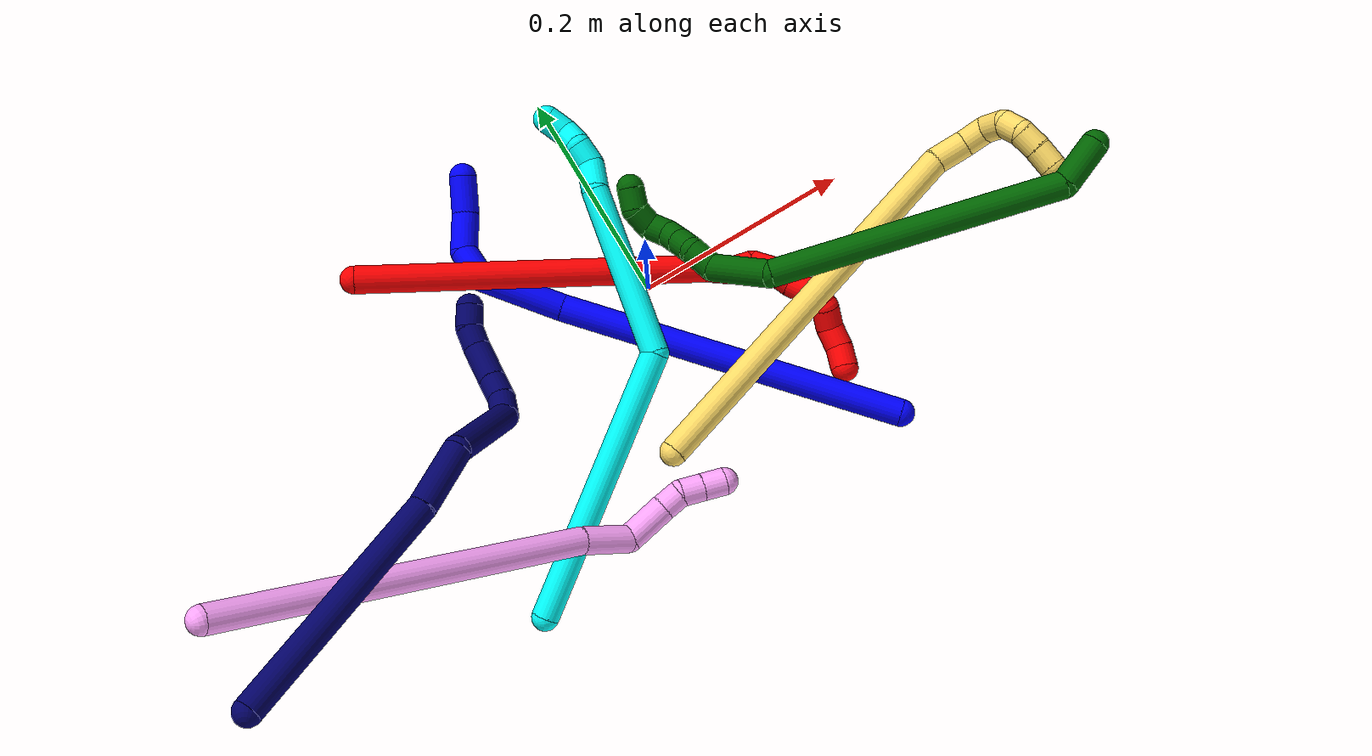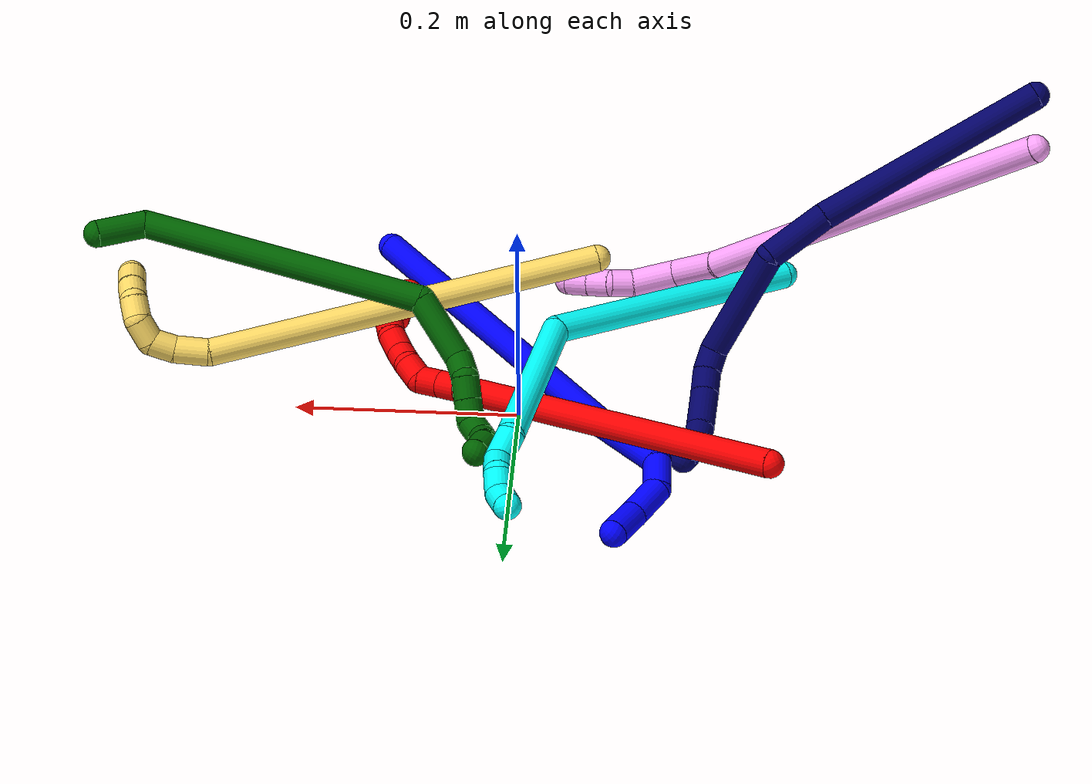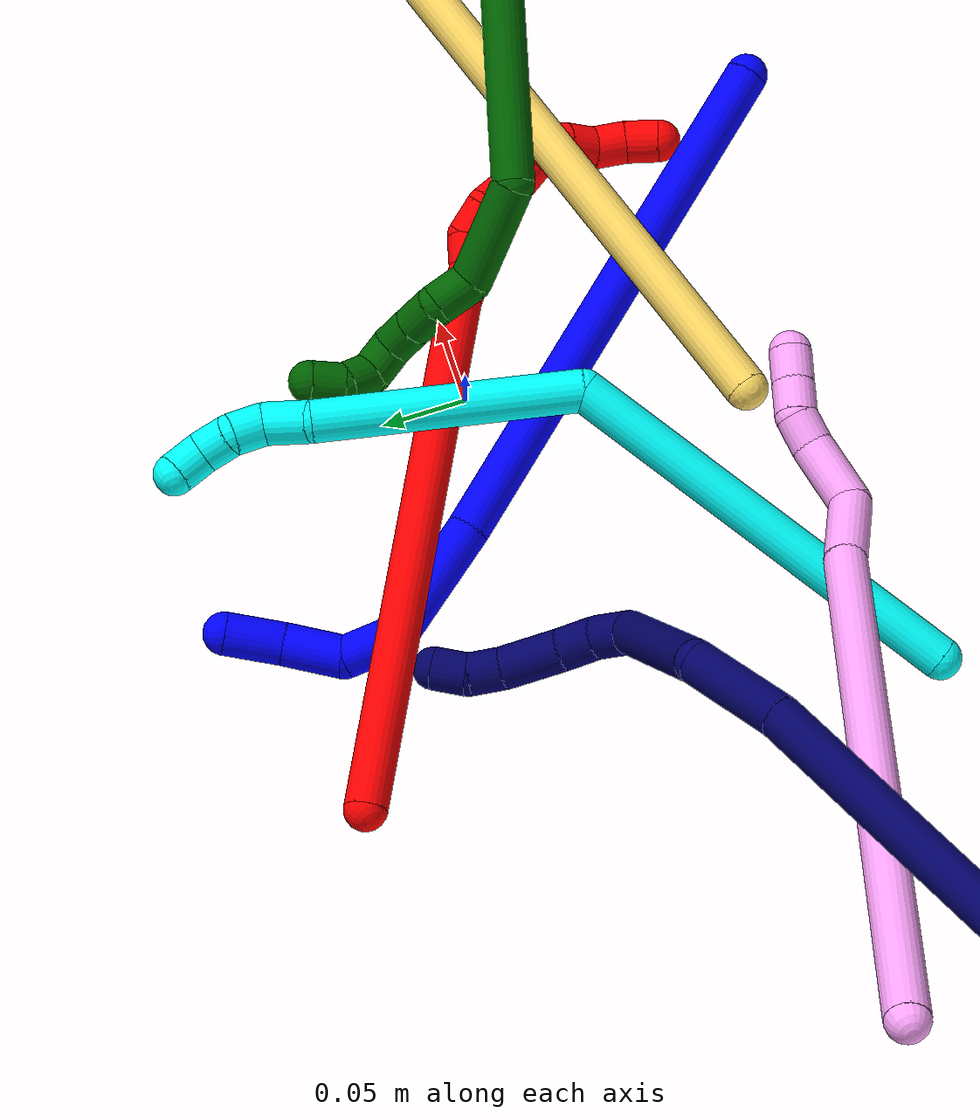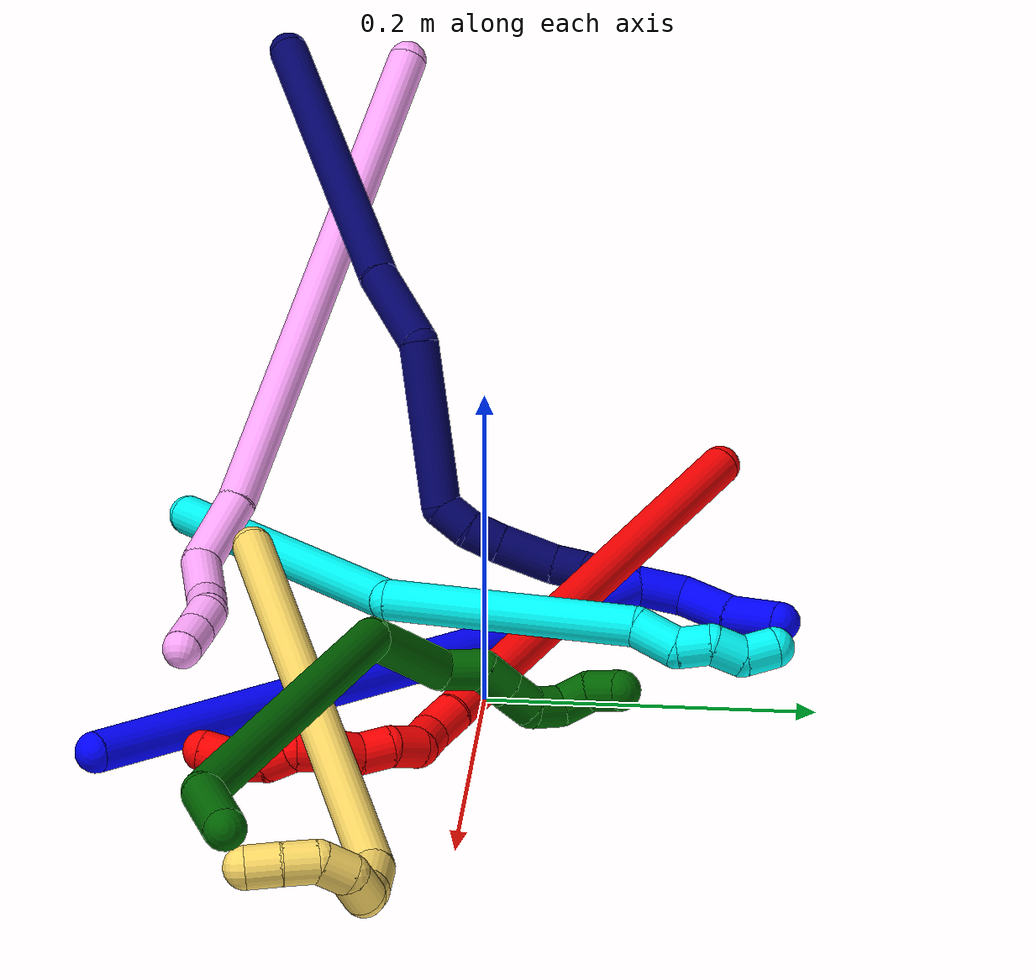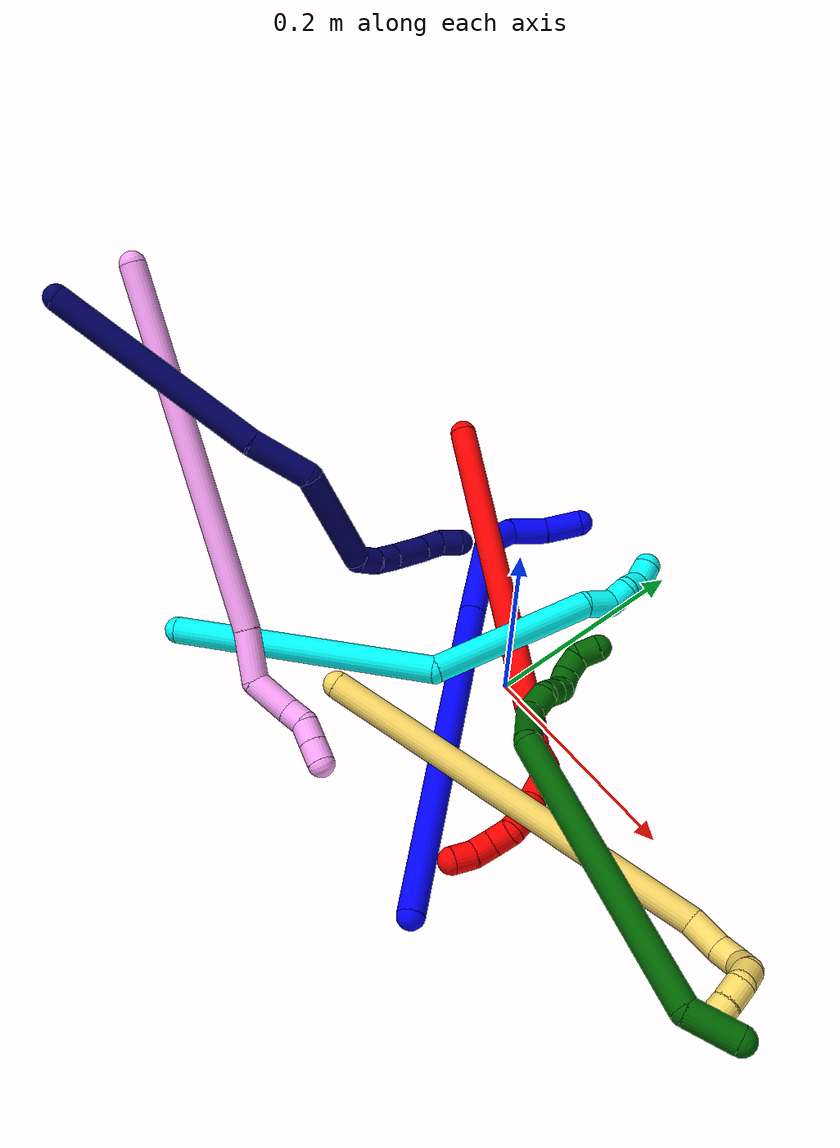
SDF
<sdf version="1.7">
 <world name="default">
  <plugin name="TubeGeneratorPlugin" filename="libtube_generator_plugin.so"/>
  <model name="photoneo_s_sensor">
   <static>1</static>
   <pose>0 0 2 1.57079 1.57079 3.14159</pose>
   <link name="link">
    <inertial><mass>0.1</mass></inertial>
    <sensor name="sensor" type="depth">
     <update_rate>30</update_rate>
     <camera>
      <horizontal_fov>1.22</horizontal_fov>
      <image><width>1920</width><height>1200</height><format>B8G8R8</format></image>
      <clip><near>0.1</near><far>4</far></clip>
      <depth_camera><output>points</output></depth_camera>
     </camera>
     <plugin name="camera_plugin" filename="libgazebo_ros_depth_camera.so">
      <baseline>0.2</baseline>
      <alwaysOn>1</alwaysOn>
      <updateRate>0.0</updateRate>
      <cameraName>camera_ir</cameraName>
      <imageTopicName>/camera/color/image_raw</imageTopicName>
      <cameraInfoTopicName>/camera/color/camera_info</cameraInfoTopicName>
      <depthImageTopicName>/camera/depth/image_raw</depthImageTopicName>
      <depthImageCameraInfoTopicName>/camera/depth/camera_info</depthImageCameraInfoTopicName>
      <pointCloudTopicName>/camera/depth/points</pointCloudTopicName>
      <frameName>fr_optical</frameName>
      <pointCloudCutoff>0.1</pointCloudCutoff>
      <pointCloudCutoffMax>2.0</pointCloudCutoffMax>
      <distortionK1>0</distortionK1>
      <distortionK2>0</distortionK2>
      <distortionK3>0</distortionK3>
      <distortionT1>0</distortionT1>
      <distortionT2>0</distortionT2>
      <CxPrime>0</CxPrime>
      <Cx>0</Cx>
      <Cy>0</Cy>
      <focalLength>0</focalLength>
      <hackBaseline>0</hackBaseline>
     </plugin>
    </sensor>
   </link>
  </model>
  <gravity>0 0 -9.8</gravity>
  <magnetic_field>6e-06 2.3e-05 -4.2e-05</magnetic_field>
  <atmosphere type="adiabatic"/>
  <physics name="default_physics" default="0" type="ode">
   <max_step_size>0.003</max_step_size>
   <real_time_factor>1</real_time_factor>
   <real_time_update_rate>1000</real_time_update_rate>
   <max_contacts>10000</max_contacts>
   <ode>
    <solver>
     <type>quick</type>
     <iters>100</iters>
     <sor>1.3</sor>
     <use_dynamic_moi_rescaling>0</use_dynamic_moi_rescaling>
    </solver>
    <constraints>
     <contact_max_correcting_vel>0</contact_max_correcting_vel>
     <contact_surface_layer>0.001</contact_surface_layer>
     <cfm>0</cfm>
     <erp>0.2</erp>
    </constraints>
   </ode>
  </physics>
  <scene><ambient>0.4 0.4 0.4 1</ambient><background>0.7 0.7 0.7 1</background><shadows>0</shadows></scene>
  <audio><device>default</device></audio>
  <spherical_coordinates>
   <surface_model>EARTH_WGS84</surface_model>
   <latitude_deg>0</latitude_deg>
   <longitude_deg>0</longitude_deg>
   <elevation>0</elevation>
   <heading_deg>0</heading_deg>
  </spherical_coordinates>
  <model name="bin">
   <static>1</static>
   <link name="bottom">
    <collision name="collision-bottom">
     <pose>0 0 -0.01 0 -0 0</pose>
     <geometry><box><size>0.8 0.6 0.02</size></box></geometry>
     <surface>
      <friction><ode><mu>100</mu><mu2>100</mu2></ode></friction>
      <contact><collide_bitmask>65535</collide_bitmask></contact>
     </surface>
    </collision>
   </link>
   <link name="west_wall">
    <collision name="collision-west_wall">
     <pose>-0.41 0 0.1 0 -0 0</pose>
     <geometry><box><size>0.02 0.6 0.2</size></box></geometry>
     <surface>
      <friction><ode><mu>100</mu><mu2>100</mu2></ode></friction>
      <contact><collide_bitmask>65535</collide_bitmask></contact>
     </surface>
    </collision>
   </link>
   <link name="east_wall">
    <collision name="collision-east_wall">
     <pose>0.41 0 0.1 0 -0 0</pose>
     <geometry><box><size>0.02 0.6 0.2</size></box></geometry>
     <surface>
      <friction><ode><mu>100</mu><mu2>100</mu2></ode></friction>
      <contact><collide_bitmask>65535</collide_bitmask></contact>
     </surface>
    </collision>
   </link>
   <link name="south_wall">
    <collision name="collision-south_wall">
     <pose>0 -0.31 0.1 0 -0 0</pose>
     <geometry><box><size>0.8 0.02 0.2</size></box></geometry>
     <surface>
      <friction><ode><mu>100</mu><mu2>100</mu2></ode></friction>
      <contact><collide_bitmask>65535</collide_bitmask></contact>
     </surface>
    </collision>
   </link>
   <link name="north_wall">
    <collision name="collision-north_wall">
     <pose>0 0.31 0.1 0 -0 0</pose>
     <geometry><box><size>0.8 0.02 0.2</size></box></geometry>
     <surface>
      <friction><ode><mu>100</mu><mu2>100</mu2></ode></friction>
      <contact><collide_bitmask>65535</collide_bitmask></contact>
     </surface>
    </collision>
   </link>
  </model>
  <model name="1">
   <static>0</static>
   <link name="1">
    <collision name="collision-cylinder-e_1_1_4">
     <pose>-0.100348 0.091365 -0.085032 -2.32031 -0.677172 1.36016</pose>
     <geometry><cylinder><radius>0.0125</radius><length>0.320299</length></cylinder></geometry>
     <surface>
      <friction><ode><mu>1.16</mu><mu2>1.16</mu2><slip1>0</slip1><slip2>0</slip2></ode></friction>
      <contact><ode><kp>1e+06</kp><kd>1</kd><max_vel>0</max_vel><min_depth>0.001</min_depth></ode></contact>
     </surface>
    </collision>
    <visual name="visual-cylinder-e_1_1_4">
     <pose>-0.100348 0.091365 -0.085032 -2.32031 -0.677172 1.36016</pose>
     <geometry><cylinder><radius>0.0125</radius><length>0.320299</length></cylinder></geometry>
     <material><ambient>0 0 1 1</ambient></material>
    </visual>
    <collision name="collision-cylinder-e_2_4_5">
     <pose>-0.229288 0.204224 -0.185956 -2.20748 -0.81902 1.42141</pose>
     <geometry><cylinder><radius>0.0125</radius><length>0.078281</length></cylinder></geometry>
     <surface>
      <friction><ode><mu>1.16</mu><mu2>1.16</mu2><slip1>0</slip1><slip2>0</slip2></ode></friction>
      <contact><ode><kp>1e+06</kp><kd>1</kd><max_vel>0</max_vel><min_depth>0.001</min_depth></ode></contact>
     </surface>
    </collision>
    <visual name="visual-cylinder-e_2_4_5">
     <pose>-0.229288 0.204224 -0.185956 -2.20748 -0.81902 1.42141</pose>
     <geometry><cylinder><radius>0.0125</radius><length>0.078281</length></cylinder></geometry>
     <material><ambient>0 0 1 1</ambient></material>
    </visual>
    <collision name="collision-cylinder-e_3_5_6">
     <pose>-0.260822 0.240498 -0.2047 -1.76139 -0.193095 0.233572</pose>
     <geometry><cylinder><radius>0.0125</radius><length>0.030677</length></cylinder></geometry>
     <surface>
      <friction><ode><mu>1.16</mu><mu2>1.16</mu2><slip1>0</slip1><slip2>0</slip2></ode></friction>
      <contact><ode><kp>1e+06</kp><kd>1</kd><max_vel>0</max_vel><min_depth>0.001</min_depth></ode></contact>
     </surface>
    </collision>
    <visual name="visual-cylinder-e_3_5_6">
     <pose>-0.260822 0.240498 -0.2047 -1.76139 -0.193095 0.233572</pose>
     <geometry><cylinder><radius>0.0125</radius><length>0.030677</length></cylinder></geometry>
     <material><ambient>0 0 1 1</ambient></material>
    </visual>
    <collision name="collision-cylinder-e_4_6_7">
     <pose>-0.261681 0.272202 -0.201793 -1.24284 0.1161 -0.083179</pose>
     <geometry><cylinder><radius>0.0125</radius><length>0.035996</length></cylinder></geometry>
     <surface>
      <friction><ode><mu>1.16</mu><mu2>1.16</mu2><slip1>0</slip1><slip2>0</slip2></ode></friction>
      <contact><ode><kp>1e+06</kp><kd>1</kd><max_vel>0</max_vel><min_depth>0.001</min_depth></ode></contact>
     </surface>
    </collision>
    <visual name="visual-cylinder-e_4_6_7">
     <pose>-0.261681 0.272202 -0.201793 -1.24284 0.1161 -0.083179</pose>
     <geometry><cylinder><radius>0.0125</radius><length>0.035996</length></cylinder></geometry>
     <material><ambient>0 0 1 1</ambient></material>
    </visual>
    <collision name="collision-cylinder-e_5_7_2">
     <pose>-0.261358 0.30494 -0.189057 -1.15523 -0.101631 0.066273</pose>
     <geometry><cylinder><radius>0.0125</radius><length>0.034748</length></cylinder></geometry>
     <surface>
      <friction><ode><mu>1.16</mu><mu2>1.16</mu2><slip1>0</slip1><slip2>0</slip2></ode></friction>
      <contact><ode><kp>1e+06</kp><kd>1</kd><max_vel>0</max_vel><min_depth>0.001</min_depth></ode></contact>
     </surface>
    </collision>
    <visual name="visual-cylinder-e_5_7_2">
     <pose>-0.261358 0.30494 -0.189057 -1.15523 -0.101631 0.066273</pose>
     <geometry><cylinder><radius>0.0125</radius><length>0.034748</length></cylinder></geometry>
     <material><ambient>0 0 1 1</ambient></material>
    </visual>
    <collision name="collision-sphere-2">
     <pose>-0.263121 0.320753 -0.182079 0 -0 0</pose>
     <geometry><sphere><radius>0.0125</radius></sphere></geometry>
     <surface>
      <friction><ode><mu>1.16</mu><mu2>1.16</mu2><slip1>0</slip1><slip2>0</slip2></ode></friction>
      <contact><ode><kp>1e+06</kp><kd>1</kd><max_vel>0</max_vel><min_depth>0.001</min_depth></ode></contact>
     </surface>
    </collision>
    <visual name="visual-sphere-2">
     <pose>-0.263121 0.320753 -0.182079 0 -0 0</pose>
     <geometry><sphere><radius>0.0125</radius></sphere></geometry>
     <material><ambient>0 0 1 1</ambient></material>
    </visual>
    <collision name="collision-sphere-7">
     <pose>-0.259596 0.289126 -0.196035 0 -0 0</pose>
     <geometry><sphere><radius>0.0125</radius></sphere></geometry>
     <surface>
      <friction><ode><mu>1.16</mu><mu2>1.16</mu2><slip1>0</slip1><slip2>0</slip2></ode></friction>
      <contact><ode><kp>1e+06</kp><kd>1</kd><max_vel>0</max_vel><min_depth>0.001</min_depth></ode></contact>
     </surface>
    </collision>
    <visual name="visual-sphere-7">
     <pose>-0.259596 0.289126 -0.196035 0 -0 0</pose>
     <geometry><sphere><radius>0.0125</radius></sphere></geometry>
     <material><ambient>0 0 1 1</ambient></material>
    </visual>
    <collision name="collision-sphere-6">
     <pose>-0.263765 0.255279 -0.207551 0 -0 0</pose>
     <geometry><sphere><radius>0.0125</radius></sphere></geometry>
     <surface>
      <friction><ode><mu>1.16</mu><mu2>1.16</mu2><slip1>0</slip1><slip2>0</slip2></ode></friction>
      <contact><ode><kp>1e+06</kp><kd>1</kd><max_vel>0</max_vel><min_depth>0.001</min_depth></ode></contact>
     </surface>
    </collision>
    <visual name="visual-sphere-6">
     <pose>-0.263765 0.255279 -0.207551 0 -0 0</pose>
     <geometry><sphere><radius>0.0125</radius></sphere></geometry>
     <material><ambient>0 0 1 1</ambient></material>
    </visual>
    <collision name="collision-sphere-5">
     <pose>-0.257879 0.225717 -0.201848 0 -0 0</pose>
     <geometry><sphere><radius>0.0125</radius></sphere></geometry>
     <surface>
      <friction><ode><mu>1.16</mu><mu2>1.16</mu2><slip1>0</slip1><slip2>0</slip2></ode></friction>
      <contact><ode><kp>1e+06</kp><kd>1</kd><max_vel>0</max_vel><min_depth>0.001</min_depth></ode></contact>
     </surface>
    </collision>
    <visual name="visual-sphere-5">
     <pose>-0.257879 0.225717 -0.201848 0 -0 0</pose>
     <geometry><sphere><radius>0.0125</radius></sphere></geometry>
     <material><ambient>0 0 1 1</ambient></material>
    </visual>
    <collision name="collision-sphere-1">
     <geometry><sphere><radius>0.0125</radius></sphere></geometry>
     <surface>
      <friction><ode><mu>1.16</mu><mu2>1.16</mu2><slip1>0</slip1><slip2>0</slip2></ode></friction>
      <contact><ode><kp>1e+06</kp><kd>1</kd><max_vel>0</max_vel><min_depth>0.001</min_depth></ode></contact>
     </surface>
    </collision>
    <visual name="visual-sphere-1">
     <geometry><sphere><radius>0.0125</radius></sphere></geometry>
     <material><ambient>0 0 1 1</ambient></material>
    </visual>
    <collision name="collision-sphere-4">
     <pose>-0.200697 0.182731 -0.170064 0 -0 0</pose>
     <geometry><sphere><radius>0.0125</radius></sphere></geometry>
     <surface>
      <friction><ode><mu>1.16</mu><mu2>1.16</mu2><slip1>0</slip1><slip2>0</slip2></ode></friction>
      <contact><ode><kp>1e+06</kp><kd>1</kd><max_vel>0</max_vel><min_depth>0.001</min_depth></ode></contact>
     </surface>
    </collision>
    <visual name="visual-sphere-4">
     <pose>-0.200697 0.182731 -0.170064 0 -0 0</pose>
     <geometry><sphere><radius>0.0125</radius></sphere></geometry>
     <material><ambient>0 0 1 1</ambient></material>
    </visual>
    <inertial>
     <pose>-0.153185 0.146046 -0.12381 0 -0 0</pose>
     <mass>0.5</mass>
     <inertia>
      <ixx>0.002572</ixx>
      <ixy>0</ixy>
      <ixz>0</ixz>
      <iyy>0.003018</iyy>
      <iyz>0</iyz>
      <izz>0.000136</izz>
     </inertia>
    </inertial>
   </link>
   <pose>0.133324 -0.217616 0.021245 -0.354526 0.805311 -0.493916</pose>
  </model>
  <model name="2">
   <static>0</static>
   <link name="2">
    <collision name="collision-cylinder-e_1_1_4">
     <pose>0.085341 -0.049845 -0.123257 2.7573 0.570647 1.97034</pose>
     <geometry><cylinder><radius>0.0125</radius><length>0.315973</length></cylinder></geometry>
     <surface>
      <friction><ode><mu>1.16</mu><mu2>1.16</mu2><slip1>0</slip1><slip2>0</slip2></ode></friction>
      <contact><ode><kp>1e+06</kp><kd>1</kd><max_vel>0</max_vel><min_depth>0.001</min_depth></ode></contact>
     </surface>
    </collision>
    <visual name="visual-cylinder-e_1_1_4">
     <pose>0.085341 -0.049845 -0.123257 2.7573 0.570647 1.97034</pose>
     <geometry><cylinder><radius>0.0125</radius><length>0.315973</length></cylinder></geometry>
     <material><ambient>1 0 0 1</ambient></material>
    </visual>
    <collision name="collision-cylinder-e_2_4_5">
     <pose>0.176341 -0.104781 -0.255337 2.61828 0.507082 1.53786</pose>
     <geometry><cylinder><radius>0.0125</radius><length>0.023308</length></cylinder></geometry>
     <surface>
      <friction><ode><mu>1.16</mu><mu2>1.16</mu2><slip1>0</slip1><slip2>0</slip2></ode></friction>
      <contact><ode><kp>1e+06</kp><kd>1</kd><max_vel>0</max_vel><min_depth>0.001</min_depth></ode></contact>
     </surface>
    </collision>
    <visual name="visual-cylinder-e_2_4_5">
     <pose>0.176341 -0.104781 -0.255337 2.61828 0.507082 1.53786</pose>
     <geometry><cylinder><radius>0.0125</radius><length>0.023308</length></cylinder></geometry>
     <material><ambient>1 0 0 1</ambient></material>
    </visual>
    <collision name="collision-cylinder-e_3_5_6">
     <pose>0.187873 -0.110285 -0.272355 3.09126 0.621266 2.98509</pose>
     <geometry><cylinder><radius>0.0125</radius><length>0.020178</length></cylinder></geometry>
     <surface>
      <friction><ode><mu>1.16</mu><mu2>1.16</mu2><slip1>0</slip1><slip2>0</slip2></ode></friction>
      <contact><ode><kp>1e+06</kp><kd>1</kd><max_vel>0</max_vel><min_depth>0.001</min_depth></ode></contact>
     </surface>
    </collision>
    <visual name="visual-cylinder-e_3_5_6">
     <pose>0.187873 -0.110285 -0.272355 3.09126 0.621266 2.98509</pose>
     <geometry><cylinder><radius>0.0125</radius><length>0.020178</length></cylinder></geometry>
     <material><ambient>1 0 0 1</ambient></material>
    </visual>
    <collision name="collision-cylinder-e_4_6_7">
     <pose>0.202708 -0.11465 -0.283628 2.23261 1.06103 1.75259</pose>
     <geometry><cylinder><radius>0.0125</radius><length>0.020537</length></cylinder></geometry>
     <surface>
      <friction><ode><mu>1.16</mu><mu2>1.16</mu2><slip1>0</slip1><slip2>0</slip2></ode></friction>
      <contact><ode><kp>1e+06</kp><kd>1</kd><max_vel>0</max_vel><min_depth>0.001</min_depth></ode></contact>
     </surface>
    </collision>
    <visual name="visual-cylinder-e_4_6_7">
     <pose>0.202708 -0.11465 -0.283628 2.23261 1.06103 1.75259</pose>
     <geometry><cylinder><radius>0.0125</radius><length>0.020537</length></cylinder></geometry>
     <material><ambient>1 0 0 1</ambient></material>
    </visual>
    <collision name="collision-cylinder-e_5_7_8">
     <pose>0.217622 -0.126114 -0.28957 1.93494 0.637239 0.892967</pose>
     <geometry><cylinder><radius>0.0125</radius><length>0.020003</length></cylinder></geometry>
     <surface>
      <friction><ode><mu>1.16</mu><mu2>1.16</mu2><slip1>0</slip1><slip2>0</slip2></ode></friction>
      <contact><ode><kp>1e+06</kp><kd>1</kd><max_vel>0</max_vel><min_depth>0.001</min_depth></ode></contact>
     </surface>
    </collision>
    <visual name="visual-cylinder-e_5_7_8">
     <pose>0.217622 -0.126114 -0.28957 1.93494 0.637239 0.892967</pose>
     <geometry><cylinder><radius>0.0125</radius><length>0.020003</length></cylinder></geometry>
     <material><ambient>1 0 0 1</ambient></material>
    </visual>
    <collision name="collision-cylinder-e_6_8_9">
     <pose>0.232478 -0.137938 -0.293884 1.89537 1.09849 1.41099</pose>
     <geometry><cylinder><radius>0.0125</radius><length>0.020001</length></cylinder></geometry>
     <surface>
      <friction><ode><mu>1.16</mu><mu2>1.16</mu2><slip1>0</slip1><slip2>0</slip2></ode></friction>
      <contact><ode><kp>1e+06</kp><kd>1</kd><max_vel>0</max_vel><min_depth>0.001</min_depth></ode></contact>
     </surface>
    </collision>
    <visual name="visual-cylinder-e_6_8_9">
     <pose>0.232478 -0.137938 -0.293884 1.89537 1.09849 1.41099</pose>
     <geometry><cylinder><radius>0.0125</radius><length>0.020001</length></cylinder></geometry>
     <material><ambient>1 0 0 1</ambient></material>
    </visual>
    <collision name="collision-cylinder-e_7_9_10">
     <pose>0.24791 -0.149807 -0.295881 1.64301 0.711077 0.759547</pose>
     <geometry><cylinder><radius>0.0125</radius><length>0.02</length></cylinder></geometry>
     <surface>
      <friction><ode><mu>1.16</mu><mu2>1.16</mu2><slip1>0</slip1><slip2>0</slip2></ode></friction>
      <contact><ode><kp>1e+06</kp><kd>1</kd><max_vel>0</max_vel><min_depth>0.001</min_depth></ode></contact>
     </surface>
    </collision>
    <visual name="visual-cylinder-e_7_9_10">
     <pose>0.24791 -0.149807 -0.295881 1.64301 0.711077 0.759547</pose>
     <geometry><cylinder><radius>0.0125</radius><length>0.02</length></cylinder></geometry>
     <material><ambient>1 0 0 1</ambient></material>
    </visual>
    <collision name="collision-cylinder-e_8_10_11">
     <pose>0.25434 -0.167335 -0.295668 1.49478 -0.009649 -0.008942</pose>
     <geometry><cylinder><radius>0.0125</radius><length>0.02</length></cylinder></geometry>
     <surface>
      <friction><ode><mu>1.16</mu><mu2>1.16</mu2><slip1>0</slip1><slip2>0</slip2></ode></friction>
      <contact><ode><kp>1e+06</kp><kd>1</kd><max_vel>0</max_vel><min_depth>0.001</min_depth></ode></contact>
     </surface>
    </collision>
    <visual name="visual-cylinder-e_8_10_11">
     <pose>0.25434 -0.167335 -0.295668 1.49478 -0.009649 -0.008942</pose>
     <geometry><cylinder><radius>0.0125</radius><length>0.02</length></cylinder></geometry>
     <material><ambient>1 0 0 1</ambient></material>
    </visual>
    <collision name="collision-cylinder-e_9_11_12">
     <pose>0.258769 -0.186005 -0.292952 1.34957 0.469681 0.378266</pose>
     <geometry><cylinder><radius>0.0125</radius><length>0.02</length></cylinder></geometry>
     <surface>
      <friction><ode><mu>1.16</mu><mu2>1.16</mu2><slip1>0</slip1><slip2>0</slip2></ode></friction>
      <contact><ode><kp>1e+06</kp><kd>1</kd><max_vel>0</max_vel><min_depth>0.001</min_depth></ode></contact>
     </surface>
    </collision>
    <visual name="visual-cylinder-e_9_11_12">
     <pose>0.258769 -0.186005 -0.292952 1.34957 0.469681 0.378266</pose>
     <geometry><cylinder><radius>0.0125</radius><length>0.02</length></cylinder></geometry>
     <material><ambient>1 0 0 1</ambient></material>
    </visual>
    <collision name="collision-cylinder-e_10_12_2">
     <pose>0.267813 -0.202467 -0.286598 1.05529 0.46873 0.276494</pose>
     <geometry><cylinder><radius>0.0125</radius><length>0.02</length></cylinder></geometry>
     <surface>
      <friction><ode><mu>1.16</mu><mu2>1.16</mu2><slip1>0</slip1><slip2>0</slip2></ode></friction>
      <contact><ode><kp>1e+06</kp><kd>1</kd><max_vel>0</max_vel><min_depth>0.001</min_depth></ode></contact>
     </surface>
    </collision>
    <visual name="visual-cylinder-e_10_12_2">
     <pose>0.267813 -0.202467 -0.286598 1.05529 0.46873 0.276494</pose>
     <geometry><cylinder><radius>0.0125</radius><length>0.02</length></cylinder></geometry>
     <material><ambient>1 0 0 1</ambient></material>
    </visual>
    <collision name="collision-sphere-2">
     <pose>0.272331 -0.210229 -0.282199 0 -0 0</pose>
     <geometry><sphere><radius>0.0125</radius></sphere></geometry>
     <surface>
      <friction><ode><mu>1.16</mu><mu2>1.16</mu2><slip1>0</slip1><slip2>0</slip2></ode></friction>
      <contact><ode><kp>1e+06</kp><kd>1</kd><max_vel>0</max_vel><min_depth>0.001</min_depth></ode></contact>
     </surface>
    </collision>
    <visual name="visual-sphere-2">
     <pose>0.272331 -0.210229 -0.282199 0 -0 0</pose>
     <geometry><sphere><radius>0.0125</radius></sphere></geometry>
     <material><ambient>1 0 0 1</ambient></material>
    </visual>
    <collision name="collision-sphere-12">
     <pose>0.263295 -0.194705 -0.290996 0 -0 0</pose>
     <geometry><sphere><radius>0.0125</radius></sphere></geometry>
     <surface>
      <friction><ode><mu>1.16</mu><mu2>1.16</mu2><slip1>0</slip1><slip2>0</slip2></ode></friction>
      <contact><ode><kp>1e+06</kp><kd>1</kd><max_vel>0</max_vel><min_depth>0.001</min_depth></ode></contact>
     </surface>
    </collision>
    <visual name="visual-sphere-12">
     <pose>0.263295 -0.194705 -0.290996 0 -0 0</pose>
     <geometry><sphere><radius>0.0125</radius></sphere></geometry>
     <material><ambient>1 0 0 1</ambient></material>
    </visual>
    <collision name="collision-sphere-11">
     <pose>0.254243 -0.177306 -0.294909 0 -0 0</pose>
     <geometry><sphere><radius>0.0125</radius></sphere></geometry>
     <surface>
      <friction><ode><mu>1.16</mu><mu2>1.16</mu2><slip1>0</slip1><slip2>0</slip2></ode></friction>
      <contact><ode><kp>1e+06</kp><kd>1</kd><max_vel>0</max_vel><min_depth>0.001</min_depth></ode></contact>
     </surface>
    </collision>
    <visual name="visual-sphere-11">
     <pose>0.254243 -0.177306 -0.294909 0 -0 0</pose>
     <geometry><sphere><radius>0.0125</radius></sphere></geometry>
     <material><ambient>1 0 0 1</ambient></material>
    </visual>
    <collision name="collision-sphere-10">
     <pose>0.254436 -0.157364 -0.296428 0 -0 0</pose>
     <geometry><sphere><radius>0.0125</radius></sphere></geometry>
     <surface>
      <friction><ode><mu>1.16</mu><mu2>1.16</mu2><slip1>0</slip1><slip2>0</slip2></ode></friction>
      <contact><ode><kp>1e+06</kp><kd>1</kd><max_vel>0</max_vel><min_depth>0.001</min_depth></ode></contact>
     </surface>
    </collision>
    <visual name="visual-sphere-10">
     <pose>0.254436 -0.157364 -0.296428 0 -0 0</pose>
     <geometry><sphere><radius>0.0125</radius></sphere></geometry>
     <material><ambient>1 0 0 1</ambient></material>
    </visual>
    <collision name="collision-sphere-9">
     <pose>0.241383 -0.14225 -0.295334 0 -0 0</pose>
     <geometry><sphere><radius>0.0125</radius></sphere></geometry>
     <surface>
      <friction><ode><mu>1.16</mu><mu2>1.16</mu2><slip1>0</slip1><slip2>0</slip2></ode></friction>
      <contact><ode><kp>1e+06</kp><kd>1</kd><max_vel>0</max_vel><min_depth>0.001</min_depth></ode></contact>
     </surface>
    </collision>
    <visual name="visual-sphere-9">
     <pose>0.241383 -0.14225 -0.295334 0 -0 0</pose>
     <geometry><sphere><radius>0.0125</radius></sphere></geometry>
     <material><ambient>1 0 0 1</ambient></material>
    </visual>
    <collision name="collision-sphere-4">
     <pose>0.170681 -0.09969 -0.246513 0 -0 0</pose>
     <geometry><sphere><radius>0.0125</radius></sphere></geometry>
     <surface>
      <friction><ode><mu>1.16</mu><mu2>1.16</mu2><slip1>0</slip1><slip2>0</slip2></ode></friction>
      <contact><ode><kp>1e+06</kp><kd>1</kd><max_vel>0</max_vel><min_depth>0.001</min_depth></ode></contact>
     </surface>
    </collision>
    <visual name="visual-sphere-4">
     <pose>0.170681 -0.09969 -0.246513 0 -0 0</pose>
     <geometry><sphere><radius>0.0125</radius></sphere></geometry>
     <material><ambient>1 0 0 1</ambient></material>
    </visual>
    <collision name="collision-sphere-1">
     <geometry><sphere><radius>0.0125</radius></sphere></geometry>
     <surface>
      <friction><ode><mu>1.16</mu><mu2>1.16</mu2><slip1>0</slip1><slip2>0</slip2></ode></friction>
      <contact><ode><kp>1e+06</kp><kd>1</kd><max_vel>0</max_vel><min_depth>0.001</min_depth></ode></contact>
     </surface>
    </collision>
    <visual name="visual-sphere-1">
     <geometry><sphere><radius>0.0125</radius></sphere></geometry>
     <material><ambient>1 0 0 1</ambient></material>
    </visual>
    <collision name="collision-sphere-8">
     <pose>0.223572 -0.133626 -0.292433 0 -0 0</pose>
     <geometry><sphere><radius>0.0125</radius></sphere></geometry>
     <surface>
      <friction><ode><mu>1.16</mu><mu2>1.16</mu2><slip1>0</slip1><slip2>0</slip2></ode></friction>
      <contact><ode><kp>1e+06</kp><kd>1</kd><max_vel>0</max_vel><min_depth>0.001</min_depth></ode></contact>
     </surface>
    </collision>
    <visual name="visual-sphere-8">
     <pose>0.223572 -0.133626 -0.292433 0 -0 0</pose>
     <geometry><sphere><radius>0.0125</radius></sphere></geometry>
     <material><ambient>1 0 0 1</ambient></material>
    </visual>
    <collision name="collision-sphere-5">
     <pose>0.182 -0.109872 -0.264161 0 -0 0</pose>
     <geometry><sphere><radius>0.0125</radius></sphere></geometry>
     <surface>
      <friction><ode><mu>1.16</mu><mu2>1.16</mu2><slip1>0</slip1><slip2>0</slip2></ode></friction>
      <contact><ode><kp>1e+06</kp><kd>1</kd><max_vel>0</max_vel><min_depth>0.001</min_depth></ode></contact>
     </surface>
    </collision>
    <visual name="visual-sphere-5">
     <pose>0.182 -0.109872 -0.264161 0 -0 0</pose>
     <geometry><sphere><radius>0.0125</radius></sphere></geometry>
     <material><ambient>1 0 0 1</ambient></material>
    </visual>
    <collision name="collision-sphere-6">
     <pose>0.193745 -0.110697 -0.280548 0 -0 0</pose>
     <geometry><sphere><radius>0.0125</radius></sphere></geometry>
     <surface>
      <friction><ode><mu>1.16</mu><mu2>1.16</mu2><slip1>0</slip1><slip2>0</slip2></ode></friction>
      <contact><ode><kp>1e+06</kp><kd>1</kd><max_vel>0</max_vel><min_depth>0.001</min_depth></ode></contact>
     </surface>
    </collision>
    <visual name="visual-sphere-6">
     <pose>0.193745 -0.110697 -0.280548 0 -0 0</pose>
     <geometry><sphere><radius>0.0125</radius></sphere></geometry>
     <material><ambient>1 0 0 1</ambient></material>
    </visual>
    <collision name="collision-sphere-7">
     <pose>0.211671 -0.118603 -0.286707 0 -0 0</pose>
     <geometry><sphere><radius>0.0125</radius></sphere></geometry>
     <surface>
      <friction><ode><mu>1.16</mu><mu2>1.16</mu2><slip1>0</slip1><slip2>0</slip2></ode></friction>
      <contact><ode><kp>1e+06</kp><kd>1</kd><max_vel>0</max_vel><min_depth>0.001</min_depth></ode></contact>
     </surface>
    </collision>
    <visual name="visual-sphere-7">
     <pose>0.211671 -0.118603 -0.286707 0 -0 0</pose>
     <geometry><sphere><radius>0.0125</radius></sphere></geometry>
     <material><ambient>1 0 0 1</ambient></material>
    </visual>
    <inertial>
     <pose>0.137218 -0.084331 -0.18262 0 -0 0</pose>
     <mass>0.5</mass>
     <inertia>
      <ixx>0.001214</ixx>
      <ixy>0</ixy>
      <ixz>0</ixz>
      <iyy>0.003489</iyy>
      <iyz>0</iyz>
      <izz>-0.000615</izz>
     </inertia>
    </inertial>
   </link>
   <pose>-0.224389 0.130142 0.061998 0.851389 -0.79288 -0.872554</pose>
  </model>
  <model name="3">
   <static>0</static>
   <link name="3">
    <collision name="collision-cylinder-e_1_1_4">
     <pose>0.062578 0.082993 -0.072812 -2.29094 0.515649 -1.05436</pose>
     <geometry><cylinder><radius>0.0125</radius><length>0.253814</length></cylinder></geometry>
     <surface>
      <friction><ode><mu>1.16</mu><mu2>1.16</mu2><slip1>0</slip1><slip2>0</slip2></ode></friction>
      <contact><ode><kp>1e+06</kp><kd>1</kd><max_vel>0</max_vel><min_depth>0.001</min_depth></ode></contact>
     </surface>
    </collision>
    <visual name="visual-cylinder-e_1_1_4">
     <pose>0.062578 0.082993 -0.072812 -2.29094 0.515649 -1.05436</pose>
     <geometry><cylinder><radius>0.0125</radius><length>0.253814</length></cylinder></geometry>
     <material><ambient>0.003922 1 0.996078 1</ambient></material>
    </visual>
    <collision name="collision-cylinder-e_2_4_5">
     <pose>0.129794 0.243758 -0.151608 -1.64759 0.059395 -0.064138</pose>
     <geometry><cylinder><radius>0.0125</radius><length>0.156279</length></cylinder></geometry>
     <surface>
      <friction><ode><mu>1.16</mu><mu2>1.16</mu2><slip1>0</slip1><slip2>0</slip2></ode></friction>
      <contact><ode><kp>1e+06</kp><kd>1</kd><max_vel>0</max_vel><min_depth>0.001</min_depth></ode></contact>
     </surface>
    </collision>
    <visual name="visual-cylinder-e_2_4_5">
     <pose>0.129794 0.243758 -0.151608 -1.64759 0.059395 -0.064138</pose>
     <geometry><cylinder><radius>0.0125</radius><length>0.156279</length></cylinder></geometry>
     <material><ambient>0.003922 1 0.996078 1</ambient></material>
    </visual>
    <collision name="collision-cylinder-e_3_5_6">
     <pose>0.132255 0.334468 -0.162806 -1.95386 -0.154847 0.228802</pose>
     <geometry><cylinder><radius>0.0125</radius><length>0.028237</length></cylinder></geometry>
     <surface>
      <friction><ode><mu>1.16</mu><mu2>1.16</mu2><slip1>0</slip1><slip2>0</slip2></ode></friction>
      <contact><ode><kp>1e+06</kp><kd>1</kd><max_vel>0</max_vel><min_depth>0.001</min_depth></ode></contact>
     </surface>
    </collision>
    <visual name="visual-cylinder-e_3_5_6">
     <pose>0.132255 0.334468 -0.162806 -1.95386 -0.154847 0.228802</pose>
     <geometry><cylinder><radius>0.0125</radius><length>0.028237</length></cylinder></geometry>
     <material><ambient>0.003922 1 0.996078 1</ambient></material>
    </visual>
    <collision name="collision-cylinder-e_4_6_7">
     <pose>0.130572 0.357536 -0.165899 -1.36443 0.047759 -0.038799</pose>
     <geometry><cylinder><radius>0.0125</radius><length>0.02072</length></cylinder></geometry>
     <surface>
      <friction><ode><mu>1.16</mu><mu2>1.16</mu2><slip1>0</slip1><slip2>0</slip2></ode></friction>
      <contact><ode><kp>1e+06</kp><kd>1</kd><max_vel>0</max_vel><min_depth>0.001</min_depth></ode></contact>
     </surface>
    </collision>
    <visual name="visual-cylinder-e_4_6_7">
     <pose>0.130572 0.357536 -0.165899 -1.36443 0.047759 -0.038799</pose>
     <geometry><cylinder><radius>0.0125</radius><length>0.02072</length></cylinder></geometry>
     <material><ambient>0.003922 1 0.996078 1</ambient></material>
    </visual>
    <collision name="collision-cylinder-e_5_7_8">
     <pose>0.126331 0.376637 -0.163985 -1.59378 -0.485514 0.496349</pose>
     <geometry><cylinder><radius>0.0125</radius><length>0.020294</length></cylinder></geometry>
     <surface>
      <friction><ode><mu>1.16</mu><mu2>1.16</mu2><slip1>0</slip1><slip2>0</slip2></ode></friction>
      <contact><ode><kp>1e+06</kp><kd>1</kd><max_vel>0</max_vel><min_depth>0.001</min_depth></ode></contact>
     </surface>
    </collision>
    <visual name="visual-cylinder-e_5_7_8">
     <pose>0.126331 0.376637 -0.163985 -1.59378 -0.485514 0.496349</pose>
     <geometry><cylinder><radius>0.0125</radius><length>0.020294</length></cylinder></geometry>
     <material><ambient>0.003922 1 0.996078 1</ambient></material>
    </visual>
    <collision name="collision-cylinder-e_6_8_2">
     <pose>0.120471 0.394554 -0.159154 -1.05794 -0.109158 0.063849</pose>
     <geometry><cylinder><radius>0.0125</radius><length>0.020655</length></cylinder></geometry>
     <surface>
      <friction><ode><mu>1.16</mu><mu2>1.16</mu2><slip1>0</slip1><slip2>0</slip2></ode></friction>
      <contact><ode><kp>1e+06</kp><kd>1</kd><max_vel>0</max_vel><min_depth>0.001</min_depth></ode></contact>
     </surface>
    </collision>
    <visual name="visual-cylinder-e_6_8_2">
     <pose>0.120471 0.394554 -0.159154 -1.05794 -0.109158 0.063849</pose>
     <geometry><cylinder><radius>0.0125</radius><length>0.020655</length></cylinder></geometry>
     <material><ambient>0.003922 1 0.996078 1</ambient></material>
    </visual>
    <collision name="collision-sphere-2">
     <pose>0.119346 0.4035 -0.154117 0 -0 0</pose>
     <geometry><sphere><radius>0.0125</radius></sphere></geometry>
     <surface>
      <friction><ode><mu>1.16</mu><mu2>1.16</mu2><slip1>0</slip1><slip2>0</slip2></ode></friction>
      <contact><ode><kp>1e+06</kp><kd>1</kd><max_vel>0</max_vel><min_depth>0.001</min_depth></ode></contact>
     </surface>
    </collision>
    <visual name="visual-sphere-2">
     <pose>0.119346 0.4035 -0.154117 0 -0 0</pose>
     <geometry><sphere><radius>0.0125</radius></sphere></geometry>
     <material><ambient>0.003922 1 0.996078 1</ambient></material>
    </visual>
    <collision name="collision-sphere-4">
     <pose>0.125156 0.165986 -0.145623 0 -0 0</pose>
     <geometry><sphere><radius>0.0125</radius></sphere></geometry>
     <surface>
      <friction><ode><mu>1.16</mu><mu2>1.16</mu2><slip1>0</slip1><slip2>0</slip2></ode></friction>
      <contact><ode><kp>1e+06</kp><kd>1</kd><max_vel>0</max_vel><min_depth>0.001</min_depth></ode></contact>
     </surface>
    </collision>
    <visual name="visual-sphere-4">
     <pose>0.125156 0.165986 -0.145623 0 -0 0</pose>
     <geometry><sphere><radius>0.0125</radius></sphere></geometry>
     <material><ambient>0.003922 1 0.996078 1</ambient></material>
    </visual>
    <collision name="collision-sphere-1">
     <geometry><sphere><radius>0.0125</radius></sphere></geometry>
     <surface>
      <friction><ode><mu>1.16</mu><mu2>1.16</mu2><slip1>0</slip1><slip2>0</slip2></ode></friction>
      <contact><ode><kp>1e+06</kp><kd>1</kd><max_vel>0</max_vel><min_depth>0.001</min_depth></ode></contact>
     </surface>
    </collision>
    <visual name="visual-sphere-1">
     <geometry><sphere><radius>0.0125</radius></sphere></geometry>
     <material><ambient>0.003922 1 0.996078 1</ambient></material>
    </visual>
    <collision name="collision-sphere-8">
     <pose>0.121596 0.385609 -0.164191 0 -0 0</pose>
     <geometry><sphere><radius>0.0125</radius></sphere></geometry>
     <surface>
      <friction><ode><mu>1.16</mu><mu2>1.16</mu2><slip1>0</slip1><slip2>0</slip2></ode></friction>
      <contact><ode><kp>1e+06</kp><kd>1</kd><max_vel>0</max_vel><min_depth>0.001</min_depth></ode></contact>
     </surface>
    </collision>
    <visual name="visual-sphere-8">
     <pose>0.121596 0.385609 -0.164191 0 -0 0</pose>
     <geometry><sphere><radius>0.0125</radius></sphere></geometry>
     <material><ambient>0.003922 1 0.996078 1</ambient></material>
    </visual>
    <collision name="collision-sphere-5">
     <pose>0.134432 0.32153 -0.157592 0 -0 0</pose>
     <geometry><sphere><radius>0.0125</radius></sphere></geometry>
     <surface>
      <friction><ode><mu>1.16</mu><mu2>1.16</mu2><slip1>0</slip1><slip2>0</slip2></ode></friction>
      <contact><ode><kp>1e+06</kp><kd>1</kd><max_vel>0</max_vel><min_depth>0.001</min_depth></ode></contact>
     </surface>
    </collision>
    <visual name="visual-sphere-5">
     <pose>0.134432 0.32153 -0.157592 0 -0 0</pose>
     <geometry><sphere><radius>0.0125</radius></sphere></geometry>
     <material><ambient>0.003922 1 0.996078 1</ambient></material>
    </visual>
    <collision name="collision-sphere-6">
     <pose>0.130077 0.347407 -0.16802 0 -0 0</pose>
     <geometry><sphere><radius>0.0125</radius></sphere></geometry>
     <surface>
      <friction><ode><mu>1.16</mu><mu2>1.16</mu2><slip1>0</slip1><slip2>0</slip2></ode></friction>
      <contact><ode><kp>1e+06</kp><kd>1</kd><max_vel>0</max_vel><min_depth>0.001</min_depth></ode></contact>
     </surface>
    </collision>
    <visual name="visual-sphere-6">
     <pose>0.130077 0.347407 -0.16802 0 -0 0</pose>
     <geometry><sphere><radius>0.0125</radius></sphere></geometry>
     <material><ambient>0.003922 1 0.996078 1</ambient></material>
    </visual>
    <collision name="collision-sphere-7">
     <pose>0.131067 0.367665 -0.163779 0 -0 0</pose>
     <geometry><sphere><radius>0.0125</radius></sphere></geometry>
     <surface>
      <friction><ode><mu>1.16</mu><mu2>1.16</mu2><slip1>0</slip1><slip2>0</slip2></ode></friction>
      <contact><ode><kp>1e+06</kp><kd>1</kd><max_vel>0</max_vel><min_depth>0.001</min_depth></ode></contact>
     </surface>
    </collision>
    <visual name="visual-sphere-7">
     <pose>0.131067 0.367665 -0.163779 0 -0 0</pose>
     <geometry><sphere><radius>0.0125</radius></sphere></geometry>
     <material><ambient>0.003922 1 0.996078 1</ambient></material>
    </visual>
    <inertial>
     <pose>0.095319 0.18361 -0.113647 0 -0 0</pose>
     <mass>0.5</mass>
     <inertia>
      <ixx>-0.000129</ixx>
      <ixy>0</ixy>
      <ixz>0</ixz>
      <iyy>-0.001054</iyy>
      <iyz>0</iyz>
      <izz>-0.001934</izz>
     </inertia>
    </inertial>
   </link>
   <pose>-0.232328 -0.209134 0.011499 -0.007114 -1.07121 -0.089359</pose>
  </model>
  <model name="4">
   <static>0</static>
   <link name="4">
    <collision name="collision-cylinder-e_1_1_4">
     <pose>0.014096 -0.025909 -0.171609 2.99175 0.081043 0.990469</pose>
     <geometry><cylinder><radius>0.0125</radius><length>0.348251</length></cylinder></geometry>
     <surface>
      <friction><ode><mu>1.16</mu><mu2>1.16</mu2><slip1>0</slip1><slip2>0</slip2></ode></friction>
      <contact><ode><kp>1e+06</kp><kd>1</kd><max_vel>0</max_vel><min_depth>0.001</min_depth></ode></contact>
     </surface>
    </collision>
    <visual name="visual-cylinder-e_1_1_4">
     <pose>0.014096 -0.025909 -0.171609 2.99175 0.081043 0.990469</pose>
     <geometry><cylinder><radius>0.0125</radius><length>0.348251</length></cylinder></geometry>
     <material><ambient>1 0.65098 0.996078 1</ambient></material>
    </visual>
    <collision name="collision-cylinder-e_2_4_5">
     <pose>0.031418 -0.058729 -0.366145 2.84879 0.133897 0.853521</pose>
     <geometry><cylinder><radius>0.0125</radius><length>0.048325</length></cylinder></geometry>
     <surface>
      <friction><ode><mu>1.16</mu><mu2>1.16</mu2><slip1>0</slip1><slip2>0</slip2></ode></friction>
      <contact><ode><kp>1e+06</kp><kd>1</kd><max_vel>0</max_vel><min_depth>0.001</min_depth></ode></contact>
     </surface>
    </collision>
    <visual name="visual-cylinder-e_2_4_5">
     <pose>0.031418 -0.058729 -0.366145 2.84879 0.133897 0.853521</pose>
     <geometry><cylinder><radius>0.0125</radius><length>0.048325</length></cylinder></geometry>
     <material><ambient>1 0.65098 0.996078 1</ambient></material>
    </visual>
    <collision name="collision-cylinder-e_3_5_6">
     <pose>0.042417 -0.057811 -0.406737 -2.72436 0.382481 -1.48159</pose>
     <geometry><cylinder><radius>0.0125</radius><length>0.041655</length></cylinder></geometry>
     <surface>
      <friction><ode><mu>1.16</mu><mu2>1.16</mu2><slip1>0</slip1><slip2>0</slip2></ode></friction>
      <contact><ode><kp>1e+06</kp><kd>1</kd><max_vel>0</max_vel><min_depth>0.001</min_depth></ode></contact>
     </surface>
    </collision>
    <visual name="visual-cylinder-e_3_5_6">
     <pose>0.042417 -0.057811 -0.406737 -2.72436 0.382481 -1.48159</pose>
     <geometry><cylinder><radius>0.0125</radius><length>0.041655</length></cylinder></geometry>
     <material><ambient>1 0.65098 0.996078 1</ambient></material>
    </visual>
    <collision name="collision-cylinder-e_4_6_7">
     <pose>0.056178 -0.046218 -0.431606 -2.66027 0.634973 -1.85861</pose>
     <geometry><cylinder><radius>0.0125</radius><length>0.02019</length></cylinder></geometry>
     <surface>
      <friction><ode><mu>1.16</mu><mu2>1.16</mu2><slip1>0</slip1><slip2>0</slip2></ode></friction>
      <contact><ode><kp>1e+06</kp><kd>1</kd><max_vel>0</max_vel><min_depth>0.001</min_depth></ode></contact>
     </surface>
    </collision>
    <visual name="visual-cylinder-e_4_6_7">
     <pose>0.056178 -0.046218 -0.431606 -2.66027 0.634973 -1.85861</pose>
     <geometry><cylinder><radius>0.0125</radius><length>0.02019</length></cylinder></geometry>
     <material><ambient>1 0.65098 0.996078 1</ambient></material>
    </visual>
    <collision name="collision-cylinder-e_5_7_8">
     <pose>0.066993 -0.043199 -0.447853 3.0596 0.488963 2.81566</pose>
     <geometry><cylinder><radius>0.0125</radius><length>0.020555</length></cylinder></geometry>
     <surface>
      <friction><ode><mu>1.16</mu><mu2>1.16</mu2><slip1>0</slip1><slip2>0</slip2></ode></friction>
      <contact><ode><kp>1e+06</kp><kd>1</kd><max_vel>0</max_vel><min_depth>0.001</min_depth></ode></contact>
     </surface>
    </collision>
    <visual name="visual-cylinder-e_5_7_8">
     <pose>0.066993 -0.043199 -0.447853 3.0596 0.488963 2.81566</pose>
     <geometry><cylinder><radius>0.0125</radius><length>0.020555</length></cylinder></geometry>
     <material><ambient>1 0.65098 0.996078 1</ambient></material>
    </visual>
    <collision name="collision-cylinder-e_6_8_2">
     <pose>0.077185 -0.044616 -0.46591 3.06693 0.535553 2.87099</pose>
     <geometry><cylinder><radius>0.0125</radius><length>0.021024</length></cylinder></geometry>
     <surface>
      <friction><ode><mu>1.16</mu><mu2>1.16</mu2><slip1>0</slip1><slip2>0</slip2></ode></friction>
      <contact><ode><kp>1e+06</kp><kd>1</kd><max_vel>0</max_vel><min_depth>0.001</min_depth></ode></contact>
     </surface>
    </collision>
    <visual name="visual-cylinder-e_6_8_2">
     <pose>0.077185 -0.044616 -0.46591 3.06693 0.535553 2.87099</pose>
     <geometry><cylinder><radius>0.0125</radius><length>0.021024</length></cylinder></geometry>
     <material><ambient>1 0.65098 0.996078 1</ambient></material>
    </visual>
    <collision name="collision-sphere-2">
     <pose>0.08255 -0.045291 -0.474926 0 -0 0</pose>
     <geometry><sphere><radius>0.0125</radius></sphere></geometry>
     <surface>
      <friction><ode><mu>1.16</mu><mu2>1.16</mu2><slip1>0</slip1><slip2>0</slip2></ode></friction>
      <contact><ode><kp>1e+06</kp><kd>1</kd><max_vel>0</max_vel><min_depth>0.001</min_depth></ode></contact>
     </surface>
    </collision>
    <visual name="visual-sphere-2">
     <pose>0.08255 -0.045291 -0.474926 0 -0 0</pose>
     <geometry><sphere><radius>0.0125</radius></sphere></geometry>
     <material><ambient>1 0.65098 0.996078 1</ambient></material>
    </visual>
    <collision name="collision-sphere-4">
     <pose>0.028192 -0.051818 -0.343219 0 -0 0</pose>
     <geometry><sphere><radius>0.0125</radius></sphere></geometry>
     <surface>
      <friction><ode><mu>1.16</mu><mu2>1.16</mu2><slip1>0</slip1><slip2>0</slip2></ode></friction>
      <contact><ode><kp>1e+06</kp><kd>1</kd><max_vel>0</max_vel><min_depth>0.001</min_depth></ode></contact>
     </surface>
    </collision>
    <visual name="visual-sphere-4">
     <pose>0.028192 -0.051818 -0.343219 0 -0 0</pose>
     <geometry><sphere><radius>0.0125</radius></sphere></geometry>
     <material><ambient>1 0.65098 0.996078 1</ambient></material>
    </visual>
    <collision name="collision-sphere-1">
     <geometry><sphere><radius>0.0125</radius></sphere></geometry>
     <surface>
      <friction><ode><mu>1.16</mu><mu2>1.16</mu2><slip1>0</slip1><slip2>0</slip2></ode></friction>
      <contact><ode><kp>1e+06</kp><kd>1</kd><max_vel>0</max_vel><min_depth>0.001</min_depth></ode></contact>
     </surface>
    </collision>
    <visual name="visual-sphere-1">
     <geometry><sphere><radius>0.0125</radius></sphere></geometry>
     <material><ambient>1 0.65098 0.996078 1</ambient></material>
    </visual>
    <collision name="collision-sphere-8">
     <pose>0.071821 -0.043942 -0.456895 0 -0 0</pose>
     <geometry><sphere><radius>0.0125</radius></sphere></geometry>
     <surface>
      <friction><ode><mu>1.16</mu><mu2>1.16</mu2><slip1>0</slip1><slip2>0</slip2></ode></friction>
      <contact><ode><kp>1e+06</kp><kd>1</kd><max_vel>0</max_vel><min_depth>0.001</min_depth></ode></contact>
     </surface>
    </collision>
    <visual name="visual-sphere-8">
     <pose>0.071821 -0.043942 -0.456895 0 -0 0</pose>
     <geometry><sphere><radius>0.0125</radius></sphere></geometry>
     <material><ambient>1 0.65098 0.996078 1</ambient></material>
    </visual>
    <collision name="collision-sphere-5">
     <pose>0.034644 -0.065641 -0.389072 0 -0 0</pose>
     <geometry><sphere><radius>0.0125</radius></sphere></geometry>
     <surface>
      <friction><ode><mu>1.16</mu><mu2>1.16</mu2><slip1>0</slip1><slip2>0</slip2></ode></friction>
      <contact><ode><kp>1e+06</kp><kd>1</kd><max_vel>0</max_vel><min_depth>0.001</min_depth></ode></contact>
     </surface>
    </collision>
    <visual name="visual-sphere-5">
     <pose>0.034644 -0.065641 -0.389072 0 -0 0</pose>
     <geometry><sphere><radius>0.0125</radius></sphere></geometry>
     <material><ambient>1 0.65098 0.996078 1</ambient></material>
    </visual>
    <collision name="collision-sphere-6">
     <pose>0.05019 -0.049981 -0.424402 0 -0 0</pose>
     <geometry><sphere><radius>0.0125</radius></sphere></geometry>
     <surface>
      <friction><ode><mu>1.16</mu><mu2>1.16</mu2><slip1>0</slip1><slip2>0</slip2></ode></friction>
      <contact><ode><kp>1e+06</kp><kd>1</kd><max_vel>0</max_vel><min_depth>0.001</min_depth></ode></contact>
     </surface>
    </collision>
    <visual name="visual-sphere-6">
     <pose>0.05019 -0.049981 -0.424402 0 -0 0</pose>
     <geometry><sphere><radius>0.0125</radius></sphere></geometry>
     <material><ambient>1 0.65098 0.996078 1</ambient></material>
    </visual>
    <collision name="collision-sphere-7">
     <pose>0.062166 -0.042456 -0.43881 0 -0 0</pose>
     <geometry><sphere><radius>0.0125</radius></sphere></geometry>
     <surface>
      <friction><ode><mu>1.16</mu><mu2>1.16</mu2><slip1>0</slip1><slip2>0</slip2></ode></friction>
      <contact><ode><kp>1e+06</kp><kd>1</kd><max_vel>0</max_vel><min_depth>0.001</min_depth></ode></contact>
     </surface>
    </collision>
    <visual name="visual-sphere-7">
     <pose>0.062166 -0.042456 -0.43881 0 -0 0</pose>
     <geometry><sphere><radius>0.0125</radius></sphere></geometry>
     <material><ambient>1 0.65098 0.996078 1</ambient></material>
    </visual>
    <inertial>
     <pose>0.024656 -0.034056 -0.24423 0 -0 0</pose>
     <mass>0.5</mass>
     <inertia>
      <ixx>0.004889</ixx>
      <ixy>0</ixy>
      <ixz>0</ixz>
      <iyy>0.00106</iyy>
      <iyz>0</iyz>
      <izz>0.000196</izz>
     </inertia>
    </inertial>
   </link>
   <pose>-0.444471 -0.08816 0.247138 0.256125 -0.881855 -0.419715</pose>
  </model>
  <model name="5">
   <static>0</static>
   <link name="5">
    <collision name="collision-cylinder-e_1_1_4">
     <pose>0.143188 0.081442 -0.075019 -2.31517 0.912549 -1.68337</pose>
     <geometry><cylinder><radius>0.0125</radius><length>0.362012</length></cylinder></geometry>
     <surface>
      <friction><ode><mu>1.16</mu><mu2>1.16</mu2><slip1>0</slip1><slip2>0</slip2></ode></friction>
      <contact><ode><kp>1e+06</kp><kd>1</kd><max_vel>0</max_vel><min_depth>0.001</min_depth></ode></contact>
     </surface>
    </collision>
    <visual name="visual-cylinder-e_1_1_4">
     <pose>0.143188 0.081442 -0.075019 -2.31517 0.912549 -1.68337</pose>
     <geometry><cylinder><radius>0.0125</radius><length>0.362012</length></cylinder></geometry>
     <material><ambient>1 0.858824 0.4 1</ambient></material>
    </visual>
    <collision name="collision-cylinder-e_2_4_5">
     <pose>0.301376 0.16606 -0.153531 -2.4037 1.26578 -2.17141</pose>
     <geometry><cylinder><radius>0.0125</radius><length>0.031452</length></cylinder></geometry>
     <surface>
      <friction><ode><mu>1.16</mu><mu2>1.16</mu2><slip1>0</slip1><slip2>0</slip2></ode></friction>
      <contact><ode><kp>1e+06</kp><kd>1</kd><max_vel>0</max_vel><min_depth>0.001</min_depth></ode></contact>
     </surface>
    </collision>
    <visual name="visual-cylinder-e_2_4_5">
     <pose>0.301376 0.16606 -0.153531 -2.4037 1.26578 -2.17141</pose>
     <geometry><cylinder><radius>0.0125</radius><length>0.031452</length></cylinder></geometry>
     <material><ambient>1 0.858824 0.4 1</ambient></material>
    </visual>
    <collision name="collision-cylinder-e_3_5_6">
     <pose>0.327429 0.171994 -0.156357 -1.33296 1.31959 -1.09574</pose>
     <geometry><cylinder><radius>0.0125</radius><length>0.022824</length></cylinder></geometry>
     <surface>
      <friction><ode><mu>1.16</mu><mu2>1.16</mu2><slip1>0</slip1><slip2>0</slip2></ode></friction>
      <contact><ode><kp>1e+06</kp><kd>1</kd><max_vel>0</max_vel><min_depth>0.001</min_depth></ode></contact>
     </surface>
    </collision>
    <visual name="visual-cylinder-e_3_5_6">
     <pose>0.327429 0.171994 -0.156357 -1.33296 1.31959 -1.09574</pose>
     <geometry><cylinder><radius>0.0125</radius><length>0.022824</length></cylinder></geometry>
     <material><ambient>1 0.858824 0.4 1</ambient></material>
    </visual>
    <collision name="collision-cylinder-e_4_6_7">
     <pose>0.347022 0.174107 -0.148205 0.085826 0.849265 0.038824</pose>
     <geometry><cylinder><radius>0.0125</radius><length>0.022746</length></cylinder></geometry>
     <surface>
      <friction><ode><mu>1.16</mu><mu2>1.16</mu2><slip1>0</slip1><slip2>0</slip2></ode></friction>
      <contact><ode><kp>1e+06</kp><kd>1</kd><max_vel>0</max_vel><min_depth>0.001</min_depth></ode></contact>
     </surface>
    </collision>
    <visual name="visual-cylinder-e_4_6_7">
     <pose>0.347022 0.174107 -0.148205 0.085826 0.849265 0.038824</pose>
     <geometry><cylinder><radius>0.0125</radius><length>0.022746</length></cylinder></geometry>
     <material><ambient>1 0.858824 0.4 1</ambient></material>
    </visual>
    <collision name="collision-cylinder-e_5_7_8">
     <pose>0.36132 0.166897 -0.13561 0.909454 0.605448 0.303048</pose>
     <geometry><cylinder><radius>0.0125</radius><length>0.020238</length></cylinder></geometry>
     <surface>
      <friction><ode><mu>1.16</mu><mu2>1.16</mu2><slip1>0</slip1><slip2>0</slip2></ode></friction>
      <contact><ode><kp>1e+06</kp><kd>1</kd><max_vel>0</max_vel><min_depth>0.001</min_depth></ode></contact>
     </surface>
    </collision>
    <visual name="visual-cylinder-e_5_7_8">
     <pose>0.36132 0.166897 -0.13561 0.909454 0.605448 0.303048</pose>
     <geometry><cylinder><radius>0.0125</radius><length>0.020238</length></cylinder></geometry>
     <material><ambient>1 0.858824 0.4 1</ambient></material>
    </visual>
    <collision name="collision-cylinder-e_6_8_9">
     <pose>0.371436 0.15124 -0.130128 1.52998 0.446663 0.429347</pose>
     <geometry><cylinder><radius>0.0125</radius><length>0.020175</length></cylinder></geometry>
     <surface>
      <friction><ode><mu>1.16</mu><mu2>1.16</mu2><slip1>0</slip1><slip2>0</slip2></ode></friction>
      <contact><ode><kp>1e+06</kp><kd>1</kd><max_vel>0</max_vel><min_depth>0.001</min_depth></ode></contact>
     </surface>
    </collision>
    <visual name="visual-cylinder-e_6_8_9">
     <pose>0.371436 0.15124 -0.130128 1.52998 0.446663 0.429347</pose>
     <geometry><cylinder><radius>0.0125</radius><length>0.020175</length></cylinder></geometry>
     <material><ambient>1 0.858824 0.4 1</ambient></material>
    </visual>
    <collision name="collision-cylinder-e_7_9_2">
     <pose>0.379335 0.132503 -0.129736 1.56859 0.351882 0.351123</pose>
     <geometry><cylinder><radius>0.0125</radius><length>0.020553</length></cylinder></geometry>
     <surface>
      <friction><ode><mu>1.16</mu><mu2>1.16</mu2><slip1>0</slip1><slip2>0</slip2></ode></friction>
      <contact><ode><kp>1e+06</kp><kd>1</kd><max_vel>0</max_vel><min_depth>0.001</min_depth></ode></contact>
     </surface>
    </collision>
    <visual name="visual-cylinder-e_7_9_2">
     <pose>0.379335 0.132503 -0.129736 1.56859 0.351882 0.351123</pose>
     <geometry><cylinder><radius>0.0125</radius><length>0.020553</length></cylinder></geometry>
     <material><ambient>1 0.858824 0.4 1</ambient></material>
    </visual>
    <collision name="collision-sphere-2">
     <pose>0.382877 0.122857 -0.129714 0 -0 0</pose>
     <geometry><sphere><radius>0.0125</radius></sphere></geometry>
     <surface>
      <friction><ode><mu>1.16</mu><mu2>1.16</mu2><slip1>0</slip1><slip2>0</slip2></ode></friction>
      <contact><ode><kp>1e+06</kp><kd>1</kd><max_vel>0</max_vel><min_depth>0.001</min_depth></ode></contact>
     </surface>
    </collision>
    <visual name="visual-sphere-2">
     <pose>0.382877 0.122857 -0.129714 0 -0 0</pose>
     <geometry><sphere><radius>0.0125</radius></sphere></geometry>
     <material><ambient>1 0.858824 0.4 1</ambient></material>
    </visual>
    <collision name="collision-sphere-9">
     <pose>0.375794 0.14215 -0.129757 0 -0 0</pose>
     <geometry><sphere><radius>0.0125</radius></sphere></geometry>
     <surface>
      <friction><ode><mu>1.16</mu><mu2>1.16</mu2><slip1>0</slip1><slip2>0</slip2></ode></friction>
      <contact><ode><kp>1e+06</kp><kd>1</kd><max_vel>0</max_vel><min_depth>0.001</min_depth></ode></contact>
     </surface>
    </collision>
    <visual name="visual-sphere-9">
     <pose>0.375794 0.14215 -0.129757 0 -0 0</pose>
     <geometry><sphere><radius>0.0125</radius></sphere></geometry>
     <material><ambient>1 0.858824 0.4 1</ambient></material>
    </visual>
    <collision name="collision-sphere-4">
     <pose>0.286376 0.162883 -0.150037 0 -0 0</pose>
     <geometry><sphere><radius>0.0125</radius></sphere></geometry>
     <surface>
      <friction><ode><mu>1.16</mu><mu2>1.16</mu2><slip1>0</slip1><slip2>0</slip2></ode></friction>
      <contact><ode><kp>1e+06</kp><kd>1</kd><max_vel>0</max_vel><min_depth>0.001</min_depth></ode></contact>
     </surface>
    </collision>
    <visual name="visual-sphere-4">
     <pose>0.286376 0.162883 -0.150037 0 -0 0</pose>
     <geometry><sphere><radius>0.0125</radius></sphere></geometry>
     <material><ambient>1 0.858824 0.4 1</ambient></material>
    </visual>
    <collision name="collision-sphere-1">
     <geometry><sphere><radius>0.0125</radius></sphere></geometry>
     <surface>
      <friction><ode><mu>1.16</mu><mu2>1.16</mu2><slip1>0</slip1><slip2>0</slip2></ode></friction>
      <contact><ode><kp>1e+06</kp><kd>1</kd><max_vel>0</max_vel><min_depth>0.001</min_depth></ode></contact>
     </surface>
    </collision>
    <visual name="visual-sphere-1">
     <geometry><sphere><radius>0.0125</radius></sphere></geometry>
     <material><ambient>1 0.858824 0.4 1</ambient></material>
    </visual>
    <collision name="collision-sphere-8">
     <pose>0.367079 0.160331 -0.1305 0 -0 0</pose>
     <geometry><sphere><radius>0.0125</radius></sphere></geometry>
     <surface>
      <friction><ode><mu>1.16</mu><mu2>1.16</mu2><slip1>0</slip1><slip2>0</slip2></ode></friction>
      <contact><ode><kp>1e+06</kp><kd>1</kd><max_vel>0</max_vel><min_depth>0.001</min_depth></ode></contact>
     </surface>
    </collision>
    <visual name="visual-sphere-8">
     <pose>0.367079 0.160331 -0.1305 0 -0 0</pose>
     <geometry><sphere><radius>0.0125</radius></sphere></geometry>
     <material><ambient>1 0.858824 0.4 1</ambient></material>
    </visual>
    <collision name="collision-sphere-5">
     <pose>0.316376 0.169237 -0.157026 0 -0 0</pose>
     <geometry><sphere><radius>0.0125</radius></sphere></geometry>
     <surface>
      <friction><ode><mu>1.16</mu><mu2>1.16</mu2><slip1>0</slip1><slip2>0</slip2></ode></friction>
      <contact><ode><kp>1e+06</kp><kd>1</kd><max_vel>0</max_vel><min_depth>0.001</min_depth></ode></contact>
     </surface>
    </collision>
    <visual name="visual-sphere-5">
     <pose>0.316376 0.169237 -0.157026 0 -0 0</pose>
     <geometry><sphere><radius>0.0125</radius></sphere></geometry>
     <material><ambient>1 0.858824 0.4 1</ambient></material>
    </visual>
    <collision name="collision-sphere-6">
     <pose>0.338483 0.174751 -0.155689 0 -0 0</pose>
     <geometry><sphere><radius>0.0125</radius></sphere></geometry>
     <surface>
      <friction><ode><mu>1.16</mu><mu2>1.16</mu2><slip1>0</slip1><slip2>0</slip2></ode></friction>
      <contact><ode><kp>1e+06</kp><kd>1</kd><max_vel>0</max_vel><min_depth>0.001</min_depth></ode></contact>
     </surface>
    </collision>
    <visual name="visual-sphere-6">
     <pose>0.338483 0.174751 -0.155689 0 -0 0</pose>
     <geometry><sphere><radius>0.0125</radius></sphere></geometry>
     <material><ambient>1 0.858824 0.4 1</ambient></material>
    </visual>
    <collision name="collision-sphere-7">
     <pose>0.355561 0.173463 -0.14072 0 -0 0</pose>
     <geometry><sphere><radius>0.0125</radius></sphere></geometry>
     <surface>
      <friction><ode><mu>1.16</mu><mu2>1.16</mu2><slip1>0</slip1><slip2>0</slip2></ode></friction>
      <contact><ode><kp>1e+06</kp><kd>1</kd><max_vel>0</max_vel><min_depth>0.001</min_depth></ode></contact>
     </surface>
    </collision>
    <visual name="visual-sphere-7">
     <pose>0.355561 0.173463 -0.14072 0 -0 0</pose>
     <geometry><sphere><radius>0.0125</radius></sphere></geometry>
     <material><ambient>1 0.858824 0.4 1</ambient></material>
    </visual>
    <inertial>
     <pose>0.198567 0.103488 -0.093925 0 -0 0</pose>
     <mass>0.5</mass>
     <inertia>
      <ixx>-0.00265</ixx>
      <ixy>0</ixy>
      <ixz>0</ixz>
      <iyy>0.000203</iyy>
      <iyz>0</iyz>
      <izz>-0.00494</izz>
     </inertia>
    </inertial>
   </link>
   <pose>-0.06167 -0.147137 0.068538 0.181417 -0.260125 -0.241865</pose>
  </model>
  <model name="6">
   <static>0</static>
   <link name="6">
    <collision name="collision-cylinder-e_1_1_4">
     <pose>-0.004652 -0.012598 -0.01821 2.53637 -0.20708 -0.64261</pose>
     <geometry><cylinder><radius>0.0125</radius><length>0.045252</length></cylinder></geometry>
     <surface>
      <friction><ode><mu>1.16</mu><mu2>1.16</mu2><slip1>0</slip1><slip2>0</slip2></ode></friction>
      <contact><ode><kp>1e+06</kp><kd>1</kd><max_vel>0</max_vel><min_depth>0.001</min_depth></ode></contact>
     </surface>
    </collision>
    <visual name="visual-cylinder-e_1_1_4">
     <pose>-0.004652 -0.012598 -0.01821 2.53637 -0.20708 -0.64261</pose>
     <geometry><cylinder><radius>0.0125</radius><length>0.045252</length></cylinder></geometry>
     <material><ambient>0 0.392157 0.003922 1</ambient></material>
    </visual>
    <collision name="collision-cylinder-e_2_4_5">
     <pose>-0.071438 -0.022137 -0.153897 -3.11556 -0.486361 3.03676</pose>
     <geometry><cylinder><radius>0.0125</radius><length>0.265865</length></cylinder></geometry>
     <surface>
      <friction><ode><mu>1.16</mu><mu2>1.16</mu2><slip1>0</slip1><slip2>0</slip2></ode></friction>
      <contact><ode><kp>1e+06</kp><kd>1</kd><max_vel>0</max_vel><min_depth>0.001</min_depth></ode></contact>
     </surface>
    </collision>
    <visual name="visual-cylinder-e_2_4_5">
     <pose>-0.071438 -0.022137 -0.153897 -3.11556 -0.486361 3.03676</pose>
     <geometry><cylinder><radius>0.0125</radius><length>0.265865</length></cylinder></geometry>
     <material><ambient>0 0.392157 0.003922 1</ambient></material>
    </visual>
    <collision name="collision-cylinder-e_3_5_6">
     <pose>-0.136695 0.000567 -0.296013 -2.46846 -0.098775 0.280684</pose>
     <geometry><cylinder><radius>0.0125</radius><length>0.063332</length></cylinder></geometry>
     <surface>
      <friction><ode><mu>1.16</mu><mu2>1.16</mu2><slip1>0</slip1><slip2>0</slip2></ode></friction>
      <contact><ode><kp>1e+06</kp><kd>1</kd><max_vel>0</max_vel><min_depth>0.001</min_depth></ode></contact>
     </surface>
    </collision>
    <visual name="visual-cylinder-e_3_5_6">
     <pose>-0.136695 0.000567 -0.296013 -2.46846 -0.098775 0.280684</pose>
     <geometry><cylinder><radius>0.0125</radius><length>0.063332</length></cylinder></geometry>
     <material><ambient>0 0.392157 0.003922 1</ambient></material>
    </visual>
    <collision name="collision-cylinder-e_4_6_7">
     <pose>-0.146468 0.03008 -0.324399 -1.93385 -0.562181 0.792804</pose>
     <geometry><cylinder><radius>0.0125</radius><length>0.024951</length></cylinder></geometry>
     <surface>
      <friction><ode><mu>1.16</mu><mu2>1.16</mu2><slip1>0</slip1><slip2>0</slip2></ode></friction>
      <contact><ode><kp>1e+06</kp><kd>1</kd><max_vel>0</max_vel><min_depth>0.001</min_depth></ode></contact>
     </surface>
    </collision>
    <visual name="visual-cylinder-e_4_6_7">
     <pose>-0.146468 0.03008 -0.324399 -1.93385 -0.562181 0.792804</pose>
     <geometry><cylinder><radius>0.0125</radius><length>0.024951</length></cylinder></geometry>
     <material><ambient>0 0.392157 0.003922 1</ambient></material>
    </visual>
    <collision name="collision-cylinder-e_5_7_8">
     <pose>-0.152197 0.048943 -0.333004 -2.0658 0.089867 -0.150455</pose>
     <geometry><cylinder><radius>0.0125</radius><length>0.020526</length></cylinder></geometry>
     <surface>
      <friction><ode><mu>1.16</mu><mu2>1.16</mu2><slip1>0</slip1><slip2>0</slip2></ode></friction>
      <contact><ode><kp>1e+06</kp><kd>1</kd><max_vel>0</max_vel><min_depth>0.001</min_depth></ode></contact>
     </surface>
    </collision>
    <visual name="visual-cylinder-e_5_7_8">
     <pose>-0.152197 0.048943 -0.333004 -2.0658 0.089867 -0.150455</pose>
     <geometry><cylinder><radius>0.0125</radius><length>0.020526</length></cylinder></geometry>
     <material><ambient>0 0.392157 0.003922 1</ambient></material>
    </visual>
    <collision name="collision-cylinder-e_6_8_9">
     <pose>-0.150606 0.066662 -0.342706 -2.07786 0.067035 -0.113843</pose>
     <geometry><cylinder><radius>0.0125</radius><length>0.020006</length></cylinder></geometry>
     <surface>
      <friction><ode><mu>1.16</mu><mu2>1.16</mu2><slip1>0</slip1><slip2>0</slip2></ode></friction>
      <contact><ode><kp>1e+06</kp><kd>1</kd><max_vel>0</max_vel><min_depth>0.001</min_depth></ode></contact>
     </surface>
    </collision>
    <visual name="visual-cylinder-e_6_8_9">
     <pose>-0.150606 0.066662 -0.342706 -2.07786 0.067035 -0.113843</pose>
     <geometry><cylinder><radius>0.0125</radius><length>0.020006</length></cylinder></geometry>
     <material><ambient>0 0.392157 0.003922 1</ambient></material>
    </visual>
    <collision name="collision-cylinder-e_7_9_10">
     <pose>-0.155092 0.081892 -0.353167 -2.28282 -0.540454 1.08813</pose>
     <geometry><cylinder><radius>0.0125</radius><length>0.020043</length></cylinder></geometry>
     <surface>
      <friction><ode><mu>1.16</mu><mu2>1.16</mu2><slip1>0</slip1><slip2>0</slip2></ode></friction>
      <contact><ode><kp>1e+06</kp><kd>1</kd><max_vel>0</max_vel><min_depth>0.001</min_depth></ode></contact>
     </surface>
    </collision>
    <visual name="visual-cylinder-e_7_9_10">
     <pose>-0.155092 0.081892 -0.353167 -2.28282 -0.540454 1.08813</pose>
     <geometry><cylinder><radius>0.0125</radius><length>0.020043</length></cylinder></geometry>
     <material><ambient>0 0.392157 0.003922 1</ambient></material>
    </visual>
    <collision name="collision-cylinder-e_8_10_11">
     <pose>-0.168824 0.093552 -0.358467 -1.50977 -1.02878 0.977308</pose>
     <geometry><cylinder><radius>0.0125</radius><length>0.020022</length></cylinder></geometry>
     <surface>
      <friction><ode><mu>1.16</mu><mu2>1.16</mu2><slip1>0</slip1><slip2>0</slip2></ode></friction>
      <contact><ode><kp>1e+06</kp><kd>1</kd><max_vel>0</max_vel><min_depth>0.001</min_depth></ode></contact>
     </surface>
    </collision>
    <visual name="visual-cylinder-e_8_10_11">
     <pose>-0.168824 0.093552 -0.358467 -1.50977 -1.02878 0.977308</pose>
     <geometry><cylinder><radius>0.0125</radius><length>0.020022</length></cylinder></geometry>
     <material><ambient>0 0.392157 0.003922 1</ambient></material>
    </visual>
    <collision name="collision-cylinder-e_9_11_2">
     <pose>-0.18227 0.106592 -0.354392 -1.1259 -0.508598 0.325164</pose>
     <geometry><cylinder><radius>0.0125</radius><length>0.020003</length></cylinder></geometry>
     <surface>
      <friction><ode><mu>1.16</mu><mu2>1.16</mu2><slip1>0</slip1><slip2>0</slip2></ode></friction>
      <contact><ode><kp>1e+06</kp><kd>1</kd><max_vel>0</max_vel><min_depth>0.001</min_depth></ode></contact>
     </surface>
    </collision>
    <visual name="visual-cylinder-e_9_11_2">
     <pose>-0.18227 0.106592 -0.354392 -1.1259 -0.508598 0.325164</pose>
     <geometry><cylinder><radius>0.0125</radius><length>0.020003</length></cylinder></geometry>
     <material><ambient>0 0.392157 0.003922 1</ambient></material>
    </visual>
    <collision name="collision-sphere-2">
     <pose>-0.187141 0.114477 -0.350633 0 -0 0</pose>
     <geometry><sphere><radius>0.0125</radius></sphere></geometry>
     <surface>
      <friction><ode><mu>1.16</mu><mu2>1.16</mu2><slip1>0</slip1><slip2>0</slip2></ode></friction>
      <contact><ode><kp>1e+06</kp><kd>1</kd><max_vel>0</max_vel><min_depth>0.001</min_depth></ode></contact>
     </surface>
    </collision>
    <visual name="visual-sphere-2">
     <pose>-0.187141 0.114477 -0.350633 0 -0 0</pose>
     <geometry><sphere><radius>0.0125</radius></sphere></geometry>
     <material><ambient>0 0.392157 0.003922 1</ambient></material>
    </visual>
    <collision name="collision-sphere-11">
     <pose>-0.1774 0.098707 -0.358152 0 -0 0</pose>
     <geometry><sphere><radius>0.0125</radius></sphere></geometry>
     <surface>
      <friction><ode><mu>1.16</mu><mu2>1.16</mu2><slip1>0</slip1><slip2>0</slip2></ode></friction>
      <contact><ode><kp>1e+06</kp><kd>1</kd><max_vel>0</max_vel><min_depth>0.001</min_depth></ode></contact>
     </surface>
    </collision>
    <visual name="visual-sphere-11">
     <pose>-0.1774 0.098707 -0.358152 0 -0 0</pose>
     <geometry><sphere><radius>0.0125</radius></sphere></geometry>
     <material><ambient>0 0.392157 0.003922 1</ambient></material>
    </visual>
    <collision name="collision-sphere-10">
     <pose>-0.160248 0.088397 -0.358782 0 -0 0</pose>
     <geometry><sphere><radius>0.0125</radius></sphere></geometry>
     <surface>
      <friction><ode><mu>1.16</mu><mu2>1.16</mu2><slip1>0</slip1><slip2>0</slip2></ode></friction>
      <contact><ode><kp>1e+06</kp><kd>1</kd><max_vel>0</max_vel><min_depth>0.001</min_depth></ode></contact>
     </surface>
    </collision>
    <visual name="visual-sphere-10">
     <pose>-0.160248 0.088397 -0.358782 0 -0 0</pose>
     <geometry><sphere><radius>0.0125</radius></sphere></geometry>
     <material><ambient>0 0.392157 0.003922 1</ambient></material>
    </visual>
    <collision name="collision-sphere-9">
     <pose>-0.149936 0.075387 -0.347553 0 -0 0</pose>
     <geometry><sphere><radius>0.0125</radius></sphere></geometry>
     <surface>
      <friction><ode><mu>1.16</mu><mu2>1.16</mu2><slip1>0</slip1><slip2>0</slip2></ode></friction>
      <contact><ode><kp>1e+06</kp><kd>1</kd><max_vel>0</max_vel><min_depth>0.001</min_depth></ode></contact>
     </surface>
    </collision>
    <visual name="visual-sphere-9">
     <pose>-0.149936 0.075387 -0.347553 0 -0 0</pose>
     <geometry><sphere><radius>0.0125</radius></sphere></geometry>
     <material><ambient>0 0.392157 0.003922 1</ambient></material>
    </visual>
    <collision name="collision-sphere-4">
     <pose>-0.009304 -0.025196 -0.036419 0 -0 0</pose>
     <geometry><sphere><radius>0.0125</radius></sphere></geometry>
     <surface>
      <friction><ode><mu>1.16</mu><mu2>1.16</mu2><slip1>0</slip1><slip2>0</slip2></ode></friction>
      <contact><ode><kp>1e+06</kp><kd>1</kd><max_vel>0</max_vel><min_depth>0.001</min_depth></ode></contact>
     </surface>
    </collision>
    <visual name="visual-sphere-4">
     <pose>-0.009304 -0.025196 -0.036419 0 -0 0</pose>
     <geometry><sphere><radius>0.0125</radius></sphere></geometry>
     <material><ambient>0 0.392157 0.003922 1</ambient></material>
    </visual>
    <collision name="collision-sphere-1">
     <geometry><sphere><radius>0.0125</radius></sphere></geometry>
     <surface>
      <friction><ode><mu>1.16</mu><mu2>1.16</mu2><slip1>0</slip1><slip2>0</slip2></ode></friction>
      <contact><ode><kp>1e+06</kp><kd>1</kd><max_vel>0</max_vel><min_depth>0.001</min_depth></ode></contact>
     </surface>
    </collision>
    <visual name="visual-sphere-1">
     <geometry><sphere><radius>0.0125</radius></sphere></geometry>
     <material><ambient>0 0.392157 0.003922 1</ambient></material>
    </visual>
    <collision name="collision-sphere-8">
     <pose>-0.151276 0.057937 -0.337859 0 -0 0</pose>
     <geometry><sphere><radius>0.0125</radius></sphere></geometry>
     <surface>
      <friction><ode><mu>1.16</mu><mu2>1.16</mu2><slip1>0</slip1><slip2>0</slip2></ode></friction>
      <contact><ode><kp>1e+06</kp><kd>1</kd><max_vel>0</max_vel><min_depth>0.001</min_depth></ode></contact>
     </surface>
    </collision>
    <visual name="visual-sphere-8">
     <pose>-0.151276 0.057937 -0.337859 0 -0 0</pose>
     <geometry><sphere><radius>0.0125</radius></sphere></geometry>
     <material><ambient>0 0.392157 0.003922 1</ambient></material>
    </visual>
    <collision name="collision-sphere-5">
     <pose>-0.133573 -0.019078 -0.271375 0 -0 0</pose>
     <geometry><sphere><radius>0.0125</radius></sphere></geometry>
     <surface>
      <friction><ode><mu>1.16</mu><mu2>1.16</mu2><slip1>0</slip1><slip2>0</slip2></ode></friction>
      <contact><ode><kp>1e+06</kp><kd>1</kd><max_vel>0</max_vel><min_depth>0.001</min_depth></ode></contact>
     </surface>
    </collision>
    <visual name="visual-sphere-5">
     <pose>-0.133573 -0.019078 -0.271375 0 -0 0</pose>
     <geometry><sphere><radius>0.0125</radius></sphere></geometry>
     <material><ambient>0 0.392157 0.003922 1</ambient></material>
    </visual>
    <collision name="collision-sphere-6">
     <pose>-0.139818 0.020213 -0.320651 0 -0 0</pose>
     <geometry><sphere><radius>0.0125</radius></sphere></geometry>
     <surface>
      <friction><ode><mu>1.16</mu><mu2>1.16</mu2><slip1>0</slip1><slip2>0</slip2></ode></friction>
      <contact><ode><kp>1e+06</kp><kd>1</kd><max_vel>0</max_vel><min_depth>0.001</min_depth></ode></contact>
     </surface>
    </collision>
    <visual name="visual-sphere-6">
     <pose>-0.139818 0.020213 -0.320651 0 -0 0</pose>
     <geometry><sphere><radius>0.0125</radius></sphere></geometry>
     <material><ambient>0 0.392157 0.003922 1</ambient></material>
    </visual>
    <collision name="collision-sphere-7">
     <pose>-0.153118 0.039948 -0.328148 0 -0 0</pose>
     <geometry><sphere><radius>0.0125</radius></sphere></geometry>
     <surface>
      <friction><ode><mu>1.16</mu><mu2>1.16</mu2><slip1>0</slip1><slip2>0</slip2></ode></friction>
      <contact><ode><kp>1e+06</kp><kd>1</kd><max_vel>0</max_vel><min_depth>0.001</min_depth></ode></contact>
     </surface>
    </collision>
    <visual name="visual-sphere-7">
     <pose>-0.153118 0.039948 -0.328148 0 -0 0</pose>
     <geometry><sphere><radius>0.0125</radius></sphere></geometry>
     <material><ambient>0 0.392157 0.003922 1</ambient></material>
    </visual>
    <inertial>
     <pose>-0.095574 0.004631 -0.207234 0 -0 0</pose>
     <mass>0.5</mass>
     <inertia>
      <ixx>-0.001214</ixx>
      <ixy>0</ixy>
      <ixz>0</ixz>
      <iyy>0.001706</iyy>
      <iyz>0</iyz>
      <izz>0.000665</izz>
     </inertia>
    </inertial>
   </link>
   <pose>0.388501 -0.109099 0.104026 -0.736142 0.856625 -0.876034</pose>
  </model>
  <model name="7">
   <static>0</static>
   <link name="7">
    <collision name="collision-cylinder-e_1_1_4">
     <pose>-0.062426 -0.012076 -0.086776 3.00332 -0.619085 -2.71513</pose>
     <geometry><cylinder><radius>0.0125</radius><length>0.215155</length></cylinder></geometry>
     <surface>
      <friction><ode><mu>1.16</mu><mu2>1.16</mu2><slip1>0</slip1><slip2>0</slip2></ode></friction>
      <contact><ode><kp>1e+06</kp><kd>1</kd><max_vel>0</max_vel><min_depth>0.001</min_depth></ode></contact>
     </surface>
    </collision>
    <visual name="visual-cylinder-e_1_1_4">
     <pose>-0.062426 -0.012076 -0.086776 3.00332 -0.619085 -2.71513</pose>
     <geometry><cylinder><radius>0.0125</radius><length>0.215155</length></cylinder></geometry>
     <material><ambient>0.003922 0 0.403922 1</ambient></material>
    </visual>
    <collision name="collision-cylinder-e_2_4_5">
     <pose>-0.138493 -0.028637 -0.200045 2.9739 -0.469756 -2.46609</pose>
     <geometry><cylinder><radius>0.0125</radius><length>0.060269</length></cylinder></geometry>
     <surface>
      <friction><ode><mu>1.16</mu><mu2>1.16</mu2><slip1>0</slip1><slip2>0</slip2></ode></friction>
      <contact><ode><kp>1e+06</kp><kd>1</kd><max_vel>0</max_vel><min_depth>0.001</min_depth></ode></contact>
     </surface>
    </collision>
    <visual name="visual-cylinder-e_2_4_5">
     <pose>-0.138493 -0.028637 -0.200045 2.9739 -0.469756 -2.46609</pose>
     <geometry><cylinder><radius>0.0125</radius><length>0.060269</length></cylinder></geometry>
     <material><ambient>0.003922 0 0.403922 1</ambient></material>
    </visual>
    <collision name="collision-cylinder-e_3_5_6">
     <pose>-0.168267 -0.0072 -0.268884 -2.59228 -0.314175 1.0242</pose>
     <geometry><cylinder><radius>0.0125</radius><length>0.104411</length></cylinder></geometry>
     <surface>
      <friction><ode><mu>1.16</mu><mu2>1.16</mu2><slip1>0</slip1><slip2>0</slip2></ode></friction>
      <contact><ode><kp>1e+06</kp><kd>1</kd><max_vel>0</max_vel><min_depth>0.001</min_depth></ode></contact>
     </surface>
    </collision>
    <visual name="visual-cylinder-e_3_5_6">
     <pose>-0.168267 -0.0072 -0.268884 -2.59228 -0.314175 1.0242</pose>
     <geometry><cylinder><radius>0.0125</radius><length>0.104411</length></cylinder></geometry>
     <material><ambient>0.003922 0 0.403922 1</ambient></material>
    </visual>
    <collision name="collision-cylinder-e_4_6_7">
     <pose>-0.182736 0.018149 -0.321954 3.08813 0.153712 2.4732</pose>
     <geometry><cylinder><radius>0.0125</radius><length>0.021736</length></cylinder></geometry>
     <surface>
      <friction><ode><mu>1.16</mu><mu2>1.16</mu2><slip1>0</slip1><slip2>0</slip2></ode></friction>
      <contact><ode><kp>1e+06</kp><kd>1</kd><max_vel>0</max_vel><min_depth>0.001</min_depth></ode></contact>
     </surface>
    </collision>
    <visual name="visual-cylinder-e_4_6_7">
     <pose>-0.182736 0.018149 -0.321954 3.08813 0.153712 2.4732</pose>
     <geometry><cylinder><radius>0.0125</radius><length>0.021736</length></cylinder></geometry>
     <material><ambient>0.003922 0 0.403922 1</ambient></material>
    </visual>
    <collision name="collision-cylinder-e_5_7_8">
     <pose>-0.176918 0.015823 -0.342557 2.96601 0.392636 2.3083</pose>
     <geometry><cylinder><radius>0.0125</radius><length>0.021717</length></cylinder></geometry>
     <surface>
      <friction><ode><mu>1.16</mu><mu2>1.16</mu2><slip1>0</slip1><slip2>0</slip2></ode></friction>
      <contact><ode><kp>1e+06</kp><kd>1</kd><max_vel>0</max_vel><min_depth>0.001</min_depth></ode></contact>
     </surface>
    </collision>
    <visual name="visual-cylinder-e_5_7_8">
     <pose>-0.176918 0.015823 -0.342557 2.96601 0.392636 2.3083</pose>
     <geometry><cylinder><radius>0.0125</radius><length>0.021717</length></cylinder></geometry>
     <material><ambient>0.003922 0 0.403922 1</ambient></material>
    </visual>
    <collision name="collision-cylinder-e_6_8_9">
     <pose>-0.165808 0.009486 -0.368606 2.86536 0.392354 1.9209</pose>
     <geometry><cylinder><radius>0.0125</radius><length>0.036381</length></cylinder></geometry>
     <surface>
      <friction><ode><mu>1.16</mu><mu2>1.16</mu2><slip1>0</slip1><slip2>0</slip2></ode></friction>
      <contact><ode><kp>1e+06</kp><kd>1</kd><max_vel>0</max_vel><min_depth>0.001</min_depth></ode></contact>
     </surface>
    </collision>
    <visual name="visual-cylinder-e_6_8_9">
     <pose>-0.165808 0.009486 -0.368606 2.86536 0.392354 1.9209</pose>
     <geometry><cylinder><radius>0.0125</radius><length>0.036381</length></cylinder></geometry>
     <material><ambient>0.003922 0 0.403922 1</ambient></material>
    </visual>
    <collision name="collision-cylinder-e_7_9_10">
     <pose>-0.155564 0.000399 -0.393114 2.64641 0.333992 1.17626</pose>
     <geometry><cylinder><radius>0.0125</radius><length>0.020059</length></cylinder></geometry>
     <surface>
      <friction><ode><mu>1.16</mu><mu2>1.16</mu2><slip1>0</slip1><slip2>0</slip2></ode></friction>
      <contact><ode><kp>1e+06</kp><kd>1</kd><max_vel>0</max_vel><min_depth>0.001</min_depth></ode></contact>
     </surface>
    </collision>
    <visual name="visual-cylinder-e_7_9_10">
     <pose>-0.155564 0.000399 -0.393114 2.64641 0.333992 1.17626</pose>
     <geometry><cylinder><radius>0.0125</radius><length>0.020059</length></cylinder></geometry>
     <material><ambient>0.003922 0 0.403922 1</ambient></material>
    </visual>
    <collision name="collision-cylinder-e_8_10_2">
     <pose>-0.152662 -0.008915 -0.410364 2.64661 -0.038036 -0.15027</pose>
     <geometry><cylinder><radius>0.0125</radius><length>0.020273</length></cylinder></geometry>
     <surface>
      <friction><ode><mu>1.16</mu><mu2>1.16</mu2><slip1>0</slip1><slip2>0</slip2></ode></friction>
      <contact><ode><kp>1e+06</kp><kd>1</kd><max_vel>0</max_vel><min_depth>0.001</min_depth></ode></contact>
     </surface>
    </collision>
    <visual name="visual-cylinder-e_8_10_2">
     <pose>-0.152662 -0.008915 -0.410364 2.64661 -0.038036 -0.15027</pose>
     <geometry><cylinder><radius>0.0125</radius><length>0.020273</length></cylinder></geometry>
     <material><ambient>0.003922 0 0.403922 1</ambient></material>
    </visual>
    <collision name="collision-sphere-2">
     <pose>-0.153047 -0.013726 -0.419277 0 -0 0</pose>
     <geometry><sphere><radius>0.0125</radius></sphere></geometry>
     <surface>
      <friction><ode><mu>1.16</mu><mu2>1.16</mu2><slip1>0</slip1><slip2>0</slip2></ode></friction>
      <contact><ode><kp>1e+06</kp><kd>1</kd><max_vel>0</max_vel><min_depth>0.001</min_depth></ode></contact>
     </surface>
    </collision>
    <visual name="visual-sphere-2">
     <pose>-0.153047 -0.013726 -0.419277 0 -0 0</pose>
     <geometry><sphere><radius>0.0125</radius></sphere></geometry>
     <material><ambient>0.003922 0 0.403922 1</ambient></material>
    </visual>
    <collision name="collision-sphere-10">
     <pose>-0.152277 -0.004103 -0.401451 0 -0 0</pose>
     <geometry><sphere><radius>0.0125</radius></sphere></geometry>
     <surface>
      <friction><ode><mu>1.16</mu><mu2>1.16</mu2><slip1>0</slip1><slip2>0</slip2></ode></friction>
      <contact><ode><kp>1e+06</kp><kd>1</kd><max_vel>0</max_vel><min_depth>0.001</min_depth></ode></contact>
     </surface>
    </collision>
    <visual name="visual-sphere-10">
     <pose>-0.152277 -0.004103 -0.401451 0 -0 0</pose>
     <geometry><sphere><radius>0.0125</radius></sphere></geometry>
     <material><ambient>0.003922 0 0.403922 1</ambient></material>
    </visual>
    <collision name="collision-sphere-9">
     <pose>-0.158852 0.004902 -0.384777 0 -0 0</pose>
     <geometry><sphere><radius>0.0125</radius></sphere></geometry>
     <surface>
      <friction><ode><mu>1.16</mu><mu2>1.16</mu2><slip1>0</slip1><slip2>0</slip2></ode></friction>
      <contact><ode><kp>1e+06</kp><kd>1</kd><max_vel>0</max_vel><min_depth>0.001</min_depth></ode></contact>
     </surface>
    </collision>
    <visual name="visual-sphere-9">
     <pose>-0.158852 0.004902 -0.384777 0 -0 0</pose>
     <geometry><sphere><radius>0.0125</radius></sphere></geometry>
     <material><ambient>0.003922 0 0.403922 1</ambient></material>
    </visual>
    <collision name="collision-sphere-4">
     <pose>-0.124852 -0.024152 -0.173552 0 -0 0</pose>
     <geometry><sphere><radius>0.0125</radius></sphere></geometry>
     <surface>
      <friction><ode><mu>1.16</mu><mu2>1.16</mu2><slip1>0</slip1><slip2>0</slip2></ode></friction>
      <contact><ode><kp>1e+06</kp><kd>1</kd><max_vel>0</max_vel><min_depth>0.001</min_depth></ode></contact>
     </surface>
    </collision>
    <visual name="visual-sphere-4">
     <pose>-0.124852 -0.024152 -0.173552 0 -0 0</pose>
     <geometry><sphere><radius>0.0125</radius></sphere></geometry>
     <material><ambient>0.003922 0 0.403922 1</ambient></material>
    </visual>
    <collision name="collision-sphere-1">
     <geometry><sphere><radius>0.0125</radius></sphere></geometry>
     <surface>
      <friction><ode><mu>1.16</mu><mu2>1.16</mu2><slip1>0</slip1><slip2>0</slip2></ode></friction>
      <contact><ode><kp>1e+06</kp><kd>1</kd><max_vel>0</max_vel><min_depth>0.001</min_depth></ode></contact>
     </surface>
    </collision>
    <visual name="visual-sphere-1">
     <geometry><sphere><radius>0.0125</radius></sphere></geometry>
     <material><ambient>0.003922 0 0.403922 1</ambient></material>
    </visual>
    <collision name="collision-sphere-8">
     <pose>-0.172763 0.01407 -0.352435 0 -0 0</pose>
     <geometry><sphere><radius>0.0125</radius></sphere></geometry>
     <surface>
      <friction><ode><mu>1.16</mu><mu2>1.16</mu2><slip1>0</slip1><slip2>0</slip2></ode></friction>
      <contact><ode><kp>1e+06</kp><kd>1</kd><max_vel>0</max_vel><min_depth>0.001</min_depth></ode></contact>
     </surface>
    </collision>
    <visual name="visual-sphere-8">
     <pose>-0.172763 0.01407 -0.352435 0 -0 0</pose>
     <geometry><sphere><radius>0.0125</radius></sphere></geometry>
     <material><ambient>0.003922 0 0.403922 1</ambient></material>
    </visual>
    <collision name="collision-sphere-5">
     <pose>-0.152134 -0.033122 -0.226538 0 -0 0</pose>
     <geometry><sphere><radius>0.0125</radius></sphere></geometry>
     <surface>
      <friction><ode><mu>1.16</mu><mu2>1.16</mu2><slip1>0</slip1><slip2>0</slip2></ode></friction>
      <contact><ode><kp>1e+06</kp><kd>1</kd><max_vel>0</max_vel><min_depth>0.001</min_depth></ode></contact>
     </surface>
    </collision>
    <visual name="visual-sphere-5">
     <pose>-0.152134 -0.033122 -0.226538 0 -0 0</pose>
     <geometry><sphere><radius>0.0125</radius></sphere></geometry>
     <material><ambient>0.003922 0 0.403922 1</ambient></material>
    </visual>
    <collision name="collision-sphere-6">
     <pose>-0.1844 0.018723 -0.31123 0 -0 0</pose>
     <geometry><sphere><radius>0.0125</radius></sphere></geometry>
     <surface>
      <friction><ode><mu>1.16</mu><mu2>1.16</mu2><slip1>0</slip1><slip2>0</slip2></ode></friction>
      <contact><ode><kp>1e+06</kp><kd>1</kd><max_vel>0</max_vel><min_depth>0.001</min_depth></ode></contact>
     </surface>
    </collision>
    <visual name="visual-sphere-6">
     <pose>-0.1844 0.018723 -0.31123 0 -0 0</pose>
     <geometry><sphere><radius>0.0125</radius></sphere></geometry>
     <material><ambient>0.003922 0 0.403922 1</ambient></material>
    </visual>
    <collision name="collision-sphere-7">
     <pose>-0.181072 0.017575 -0.332679 0 -0 0</pose>
     <geometry><sphere><radius>0.0125</radius></sphere></geometry>
     <surface>
      <friction><ode><mu>1.16</mu><mu2>1.16</mu2><slip1>0</slip1><slip2>0</slip2></ode></friction>
      <contact><ode><kp>1e+06</kp><kd>1</kd><max_vel>0</max_vel><min_depth>0.001</min_depth></ode></contact>
     </surface>
    </collision>
    <visual name="visual-sphere-7">
     <pose>-0.181072 0.017575 -0.332679 0 -0 0</pose>
     <geometry><sphere><radius>0.0125</radius></sphere></geometry>
     <material><ambient>0.003922 0 0.403922 1</ambient></material>
    </visual>
    <inertial>
     <pose>-0.118817 -0.008331 -0.205706 0 -0 0</pose>
     <mass>0.5</mass>
     <inertia>
      <ixx>-0.000807</ixx>
      <ixy>0</ixy>
      <ixz>0</ixz>
      <iyy>0.000567</iyy>
      <iyz>0</iyz>
      <izz>0.000541</izz>
     </inertia>
    </inertial>
   </link>
   <pose>-0.447119 -0.166208 0.249813 -0.938766 -0.004415 2.6484</pose>
  </model>
 </world>
</sdf>
